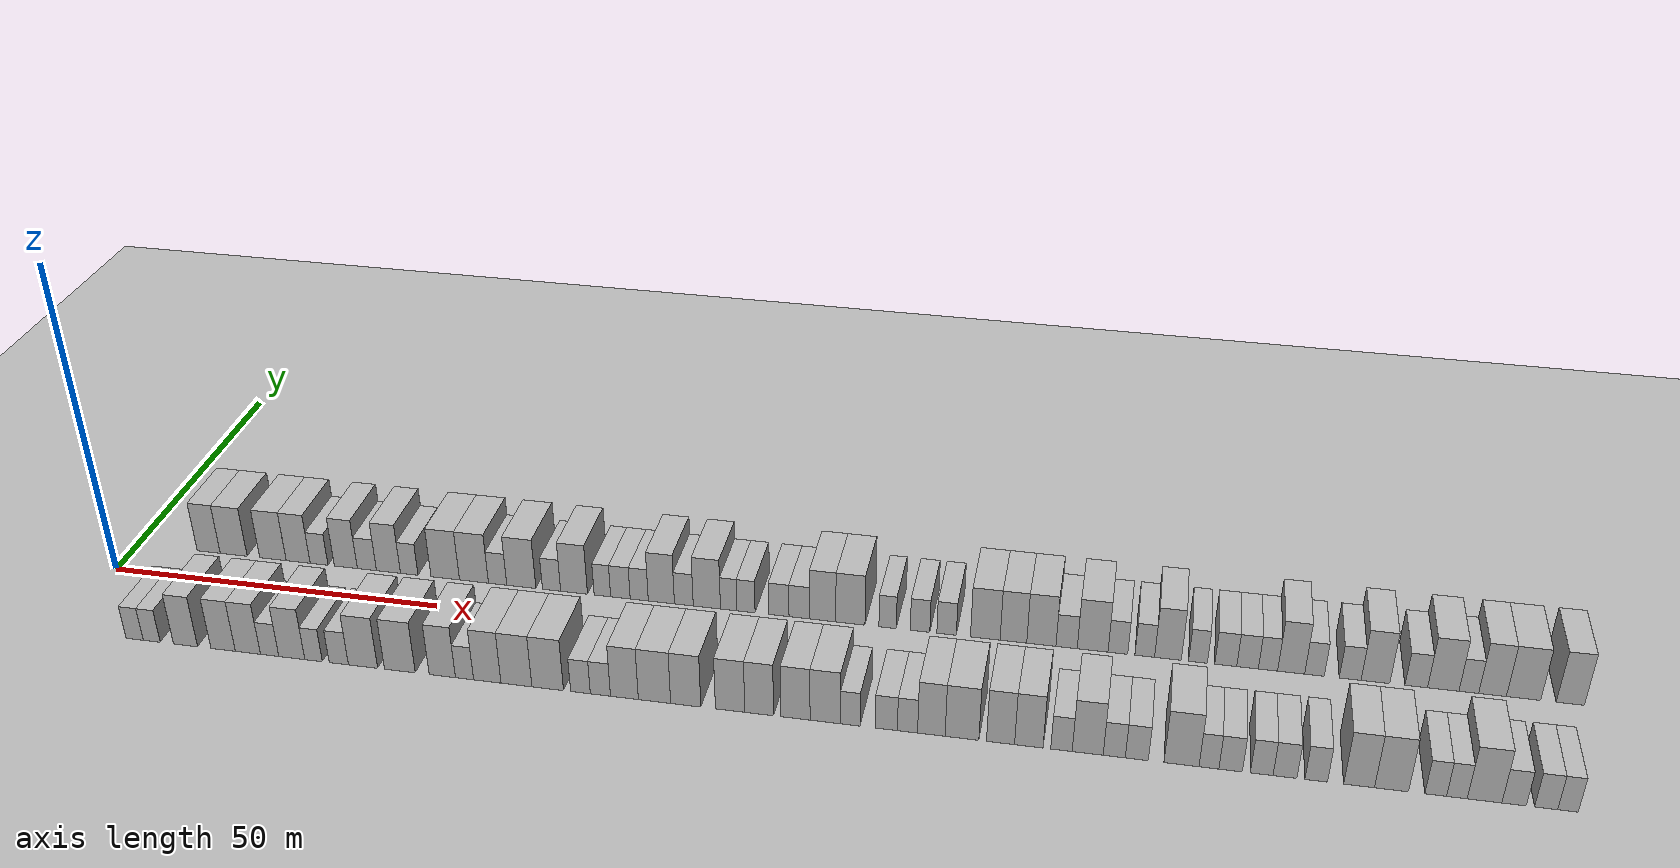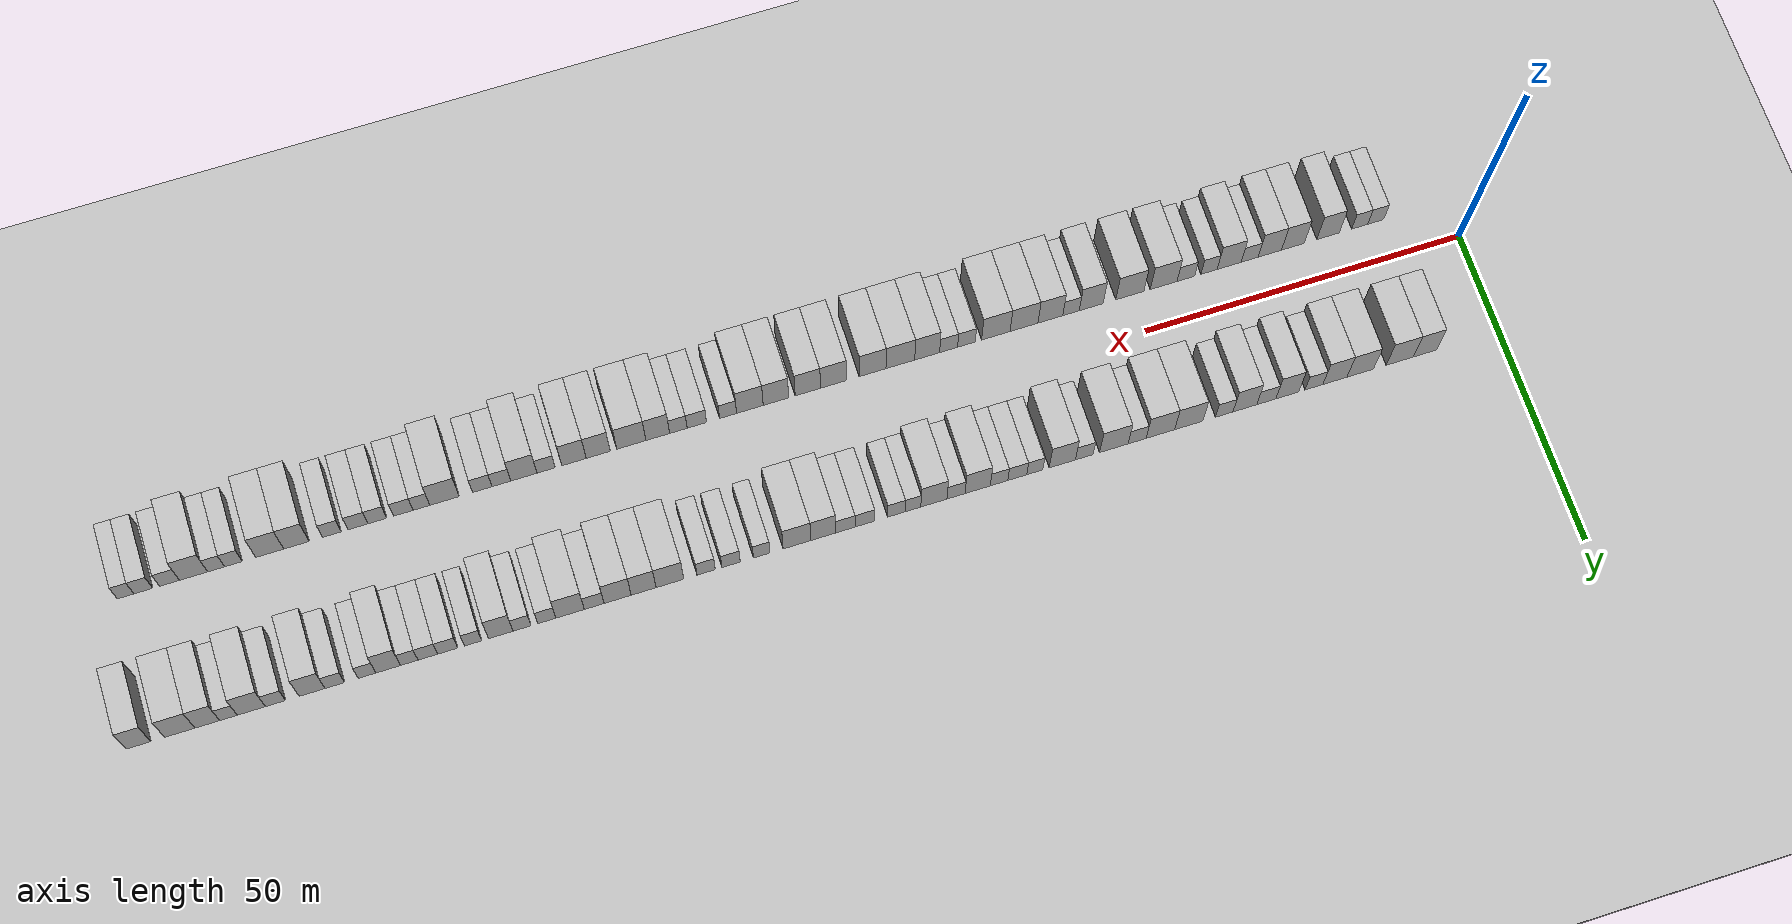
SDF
<?xml version="1.0" encoding="utf-8"?>

<sdf version="1.6">

   <world name="default">

      <gui fullscreen="0">

         <camera name="user_camera">

            <pose>-15 0 4.57585 0 0 0</pose>

            <view_controller>orbit</view_controller>

         </camera>

      </gui>

      <scene>

         <sky>

           <clouds>

             <speed>12</speed>

           </clouds>

         </sky>

         <ambient>0.4 0.4 0.4 1</ambient>

         <background>0.7 0.7 0.7 1</background>

         <shadows>1</shadows>

      </scene>

      <gravity>0 0 -9.8066</gravity>

      <magnetic_field>6e-06 2.3e-05 -4.2e-05</magnetic_field>

      <physics default="0" name="default_physics" type="ode">

         <ode>

            <solver>

               <type>quick</type>

               <iters>10</iters>

               <sor>1.0</sor>

               <use_dynamic_moi_rescaling>0</use_dynamic_moi_rescaling>

            </solver>

            <constraints>

               <cfm>0</cfm>

               <erp>0.2</erp>

               <contact_max_correcting_vel>100</contact_max_correcting_vel>

               <contact_surface_layer>0.001</contact_surface_layer>

            </constraints>

         </ode>

         <max_step_size>0.004</max_step_size>

         <real_time_factor>1</real_time_factor>

         <real_time_update_rate>250</real_time_update_rate>

      </physics>

      <light name="sun" type="directional">

         <cast_shadows>1</cast_shadows>

         <pose>0 0 10 0 0 0</pose>

         <diffuse>0.8 0.8 0.8 1</diffuse>

         <specular>0.2 0.2 0.2 1</specular>

         <attenuation>

            <range>1000</range>

            <constant>0.9</constant>

            <linear>0.01</linear>

            <quadratic>0.001</quadratic>

         </attenuation>

         <direction>-0.5 0.1 -0.9</direction>

      </light>

      <include>

         <name>ground_plane_1</name>

         <uri>model://HANNAS_ground_plane</uri>

         <pose>0 0 0  0 0 0</pose>

      </include>

      <include>

         <name>ground_plane_2</name>

         <uri>model://HANNAS_ground_plane</uri>

         <pose>100 0 0  0 0 0</pose>

      </include>

      <model name="building_1">

         <static>1</static>

         <pose frame="">11.8461 11.0000 0 0.000000 0.000000 1.570796</pose>

         <link name="link">

            <pose frame="">0 0 4.50 0 0 0</pose>

            <collision name="collision">

               <geometry>

                  <box>

                     <size>10.0000 3.6923 9.0000</size>

                  </box>

               </geometry>

               <max_contacts>10</max_contacts>

               <surface>

                  <contact>

                     <ode/>

                  </contact>

                  <bounce/>

                  <friction>

                     <torsional>

                        <ode/>

                     </torsional>

                     <ode/>

                  </friction>

               </surface>

            </collision>

            <visual name="visual">

               <cast_shadows>0</cast_shadows>

               <geometry>

                  <box>

                     <size>10.0000 3.6923 9.0000</size>

                  </box>

               </geometry>

               <material>

                  <script>

                     <uri>model://HANNAS_wall/materials/scripts</uri>

                     <uri>model://HANNAS_wall/materials/textures</uri>

                     <name>vrc/HANNAS_wall</name>

                  </script>

               </material>

            </visual>

            <self_collide>0</self_collide>

            <enable_wind>0</enable_wind>

            <kinematic>0</kinematic>

         </link>

      </model>

      <model name="building_2">

         <static>1</static>

         <pose frame="">15.8507 11.0000 0 0.000000 0.000000 1.570796</pose>

         <link name="link">

            <pose frame="">0 0 4.50 0 0 0</pose>

            <collision name="collision">

               <geometry>

                  <box>

                     <size>10.0000 4.3167 9.0000</size>

                  </box>

               </geometry>

               <max_contacts>10</max_contacts>

               <surface>

                  <contact>

                     <ode/>

                  </contact>

                  <bounce/>

                  <friction>

                     <torsional>

                        <ode/>

                     </torsional>

                     <ode/>

                  </friction>

               </surface>

            </collision>

            <visual name="visual">

               <cast_shadows>0</cast_shadows>

               <geometry>

                  <box>

                     <size>10.0000 4.3167 9.0000</size>

                  </box>

               </geometry>

               <material>

                  <script>

                     <uri>model://HANNAS_wall/materials/scripts</uri>

                     <uri>model://HANNAS_wall/materials/textures</uri>

                     <name>vrc/HANNAS_wall</name>

                  </script>

               </material>

            </visual>

            <self_collide>0</self_collide>

            <enable_wind>0</enable_wind>

            <kinematic>0</kinematic>

         </link>

      </model>

      <model name="building_3">

         <static>1</static>

         <pose frame="">22.1099 11.0000 0 0.000000 0.000000 1.570796</pose>

         <link name="link">

            <pose frame="">0 0 4.50 0 0 0</pose>

            <collision name="collision">

               <geometry>

                  <box>

                     <size>10.0000 4.2018 9.0000</size>

                  </box>

               </geometry>

               <max_contacts>10</max_contacts>

               <surface>

                  <contact>

                     <ode/>

                  </contact>

                  <bounce/>

                  <friction>

                     <torsional>

                        <ode/>

                     </torsional>

                     <ode/>

                  </friction>

               </surface>

            </collision>

            <visual name="visual">

               <cast_shadows>0</cast_shadows>

               <geometry>

                  <box>

                     <size>10.0000 4.2018 9.0000</size>

                  </box>

               </geometry>

               <material>

                  <script>

                     <uri>model://HANNAS_wall/materials/scripts</uri>

                     <uri>model://HANNAS_wall/materials/textures</uri>

                     <name>vrc/HANNAS_wall</name>

                  </script>

               </material>

            </visual>

            <self_collide>0</self_collide>

            <enable_wind>0</enable_wind>

            <kinematic>0</kinematic>

         </link>

      </model>

      <model name="building_4">

         <static>1</static>

         <pose frame="">26.1107 11.0000 0 0.000000 0.000000 1.570796</pose>

         <link name="link">

            <pose frame="">0 0 4.50 0 0 0</pose>

            <collision name="collision">

               <geometry>

                  <box>

                     <size>10.0000 3.7997 9.0000</size>

                  </box>

               </geometry>

               <max_contacts>10</max_contacts>

               <surface>

                  <contact>

                     <ode/>

                  </contact>

                  <bounce/>

                  <friction>

                     <torsional>

                        <ode/>

                     </torsional>

                     <ode/>

                  </friction>

               </surface>

            </collision>

            <visual name="visual">

               <cast_shadows>0</cast_shadows>

               <geometry>

                  <box>

                     <size>10.0000 3.7997 9.0000</size>

                  </box>

               </geometry>

               <material>

                  <script>

                     <uri>model://HANNAS_wall/materials/scripts</uri>

                     <uri>model://HANNAS_wall/materials/textures</uri>

                     <name>vrc/HANNAS_wall</name>

                  </script>

               </material>

            </visual>

            <self_collide>0</self_collide>

            <enable_wind>0</enable_wind>

            <kinematic>0</kinematic>

         </link>

      </model>

      <model name="building_5">

         <static>1</static>

         <pose frame="">29.4177 11.0000 0 0.000000 0.000000 1.570796</pose>

         <link name="link">

            <pose frame="">0 0 3.00 0 0 0</pose>

            <collision name="collision">

               <geometry>

                  <box>

                     <size>10.0000 2.8143 6.0000</size>

                  </box>

               </geometry>

               <max_contacts>10</max_contacts>

               <surface>

                  <contact>

                     <ode/>

                  </contact>

                  <bounce/>

                  <friction>

                     <torsional>

                        <ode/>

                     </torsional>

                     <ode/>

                  </friction>

               </surface>

            </collision>

            <visual name="visual">

               <cast_shadows>0</cast_shadows>

               <geometry>

                  <box>

                     <size>10.0000 2.8143 6.0000</size>

                  </box>

               </geometry>

               <material>

                  <script>

                     <uri>model://HANNAS_wall/materials/scripts</uri>

                     <uri>model://HANNAS_wall/materials/textures</uri>

                     <name>vrc/HANNAS_wall</name>

                  </script>

               </material>

            </visual>

            <self_collide>0</self_collide>

            <enable_wind>0</enable_wind>

            <kinematic>0</kinematic>

         </link>

      </model>

      <model name="building_6">

         <static>1</static>

         <pose frame="">33.6269 11.0000 0 0.000000 0.000000 1.570796</pose>

         <link name="link">

            <pose frame="">0 0 4.50 0 0 0</pose>

            <collision name="collision">

               <geometry>

                  <box>

                     <size>10.0000 3.6042 9.0000</size>

                  </box>

               </geometry>

               <max_contacts>10</max_contacts>

               <surface>

                  <contact>

                     <ode/>

                  </contact>

                  <bounce/>

                  <friction>

                     <torsional>

                        <ode/>

                     </torsional>

                     <ode/>

                  </friction>

               </surface>

            </collision>

            <visual name="visual">

               <cast_shadows>0</cast_shadows>

               <geometry>

                  <box>

                     <size>10.0000 3.6042 9.0000</size>

                  </box>

               </geometry>

               <material>

                  <script>

                     <uri>model://HANNAS_wall/materials/scripts</uri>

                     <uri>model://HANNAS_wall/materials/textures</uri>

                     <name>vrc/HANNAS_wall</name>

                  </script>

               </material>

            </visual>

            <self_collide>0</self_collide>

            <enable_wind>0</enable_wind>

            <kinematic>0</kinematic>

         </link>

      </model>

      <model name="building_7">

         <static>1</static>

         <pose frame="">36.9258 11.0000 0 0.000000 0.000000 1.570796</pose>

         <link name="link">

            <pose frame="">0 0 3.00 0 0 0</pose>

            <collision name="collision">

               <geometry>

                  <box>

                     <size>10.0000 2.9936 6.0000</size>

                  </box>

               </geometry>

               <max_contacts>10</max_contacts>

               <surface>

                  <contact>

                     <ode/>

                  </contact>

                  <bounce/>

                  <friction>

                     <torsional>

                        <ode/>

                     </torsional>

                     <ode/>

                  </friction>

               </surface>

            </collision>

            <visual name="visual">

               <cast_shadows>0</cast_shadows>

               <geometry>

                  <box>

                     <size>10.0000 2.9936 6.0000</size>

                  </box>

               </geometry>

               <material>

                  <script>

                     <uri>model://HANNAS_wall/materials/scripts</uri>

                     <uri>model://HANNAS_wall/materials/textures</uri>

                     <name>vrc/HANNAS_wall</name>

                  </script>

               </material>

            </visual>

            <self_collide>0</self_collide>

            <enable_wind>0</enable_wind>

            <kinematic>0</kinematic>

         </link>

      </model>

      <model name="building_8">

         <static>1</static>

         <pose frame="">40.2935 11.0000 0 0.000000 0.000000 1.570796</pose>

         <link name="link">

            <pose frame="">0 0 4.50 0 0 0</pose>

            <collision name="collision">

               <geometry>

                  <box>

                     <size>10.0000 3.7417 9.0000</size>

                  </box>

               </geometry>

               <max_contacts>10</max_contacts>

               <surface>

                  <contact>

                     <ode/>

                  </contact>

                  <bounce/>

                  <friction>

                     <torsional>

                        <ode/>

                     </torsional>

                     <ode/>

                  </friction>

               </surface>

            </collision>

            <visual name="visual">

               <cast_shadows>0</cast_shadows>

               <geometry>

                  <box>

                     <size>10.0000 3.7417 9.0000</size>

                  </box>

               </geometry>

               <material>

                  <script>

                     <uri>model://HANNAS_wall/materials/scripts</uri>

                     <uri>model://HANNAS_wall/materials/textures</uri>

                     <name>vrc/HANNAS_wall</name>

                  </script>

               </material>

            </visual>

            <self_collide>0</self_collide>

            <enable_wind>0</enable_wind>

            <kinematic>0</kinematic>

         </link>

      </model>

      <model name="building_9">

         <static>1</static>

         <pose frame="">43.5288 11.0000 0 0.000000 0.000000 1.570796</pose>

         <link name="link">

            <pose frame="">0 0 3.00 0 0 0</pose>

            <collision name="collision">

               <geometry>

                  <box>

                     <size>10.0000 2.7289 6.0000</size>

                  </box>

               </geometry>

               <max_contacts>10</max_contacts>

               <surface>

                  <contact>

                     <ode/>

                  </contact>

                  <bounce/>

                  <friction>

                     <torsional>

                        <ode/>

                     </torsional>

                     <ode/>

                  </friction>

               </surface>

            </collision>

            <visual name="visual">

               <cast_shadows>0</cast_shadows>

               <geometry>

                  <box>

                     <size>10.0000 2.7289 6.0000</size>

                  </box>

               </geometry>

               <material>

                  <script>

                     <uri>model://HANNAS_wall/materials/scripts</uri>

                     <uri>model://HANNAS_wall/materials/textures</uri>

                     <name>vrc/HANNAS_wall</name>

                  </script>

               </material>

            </visual>

            <self_collide>0</self_collide>

            <enable_wind>0</enable_wind>

            <kinematic>0</kinematic>

         </link>

      </model>

      <model name="building_10">

         <static>1</static>

         <pose frame="">49.0889 11.0000 0 0.000000 0.000000 1.570796</pose>

         <link name="link">

            <pose frame="">0 0 4.50 0 0 0</pose>

            <collision name="collision">

               <geometry>

                  <box>

                     <size>10.0000 4.3914 9.0000</size>

                  </box>

               </geometry>

               <max_contacts>10</max_contacts>

               <surface>

                  <contact>

                     <ode/>

                  </contact>

                  <bounce/>

                  <friction>

                     <torsional>

                        <ode/>

                     </torsional>

                     <ode/>

                  </friction>

               </surface>

            </collision>

            <visual name="visual">

               <cast_shadows>0</cast_shadows>

               <geometry>

                  <box>

                     <size>10.0000 4.3914 9.0000</size>

                  </box>

               </geometry>

               <material>

                  <script>

                     <uri>model://HANNAS_wall/materials/scripts</uri>

                     <uri>model://HANNAS_wall/materials/textures</uri>

                     <name>vrc/HANNAS_wall</name>

                  </script>

               </material>

            </visual>

            <self_collide>0</self_collide>

            <enable_wind>0</enable_wind>

            <kinematic>0</kinematic>

         </link>

      </model>

      <model name="building_11">

         <static>1</static>

         <pose frame="">53.5104 11.0000 0 0.000000 0.000000 1.570796</pose>

         <link name="link">

            <pose frame="">0 0 4.50 0 0 0</pose>

            <collision name="collision">

               <geometry>

                  <box>

                     <size>10.0000 4.4515 9.0000</size>

                  </box>

               </geometry>

               <max_contacts>10</max_contacts>

               <surface>

                  <contact>

                     <ode/>

                  </contact>

                  <bounce/>

                  <friction>

                     <torsional>

                        <ode/>

                     </torsional>

                     <ode/>

                  </friction>

               </surface>

            </collision>

            <visual name="visual">

               <cast_shadows>0</cast_shadows>

               <geometry>

                  <box>

                     <size>10.0000 4.4515 9.0000</size>

                  </box>

               </geometry>

               <material>

                  <script>

                     <uri>model://HANNAS_wall/materials/scripts</uri>

                     <uri>model://HANNAS_wall/materials/textures</uri>

                     <name>vrc/HANNAS_wall</name>

                  </script>

               </material>

            </visual>

            <self_collide>0</self_collide>

            <enable_wind>0</enable_wind>

            <kinematic>0</kinematic>

         </link>

      </model>

      <model name="building_12">

         <static>1</static>

         <pose frame="">57.1330 11.0000 0 0.000000 0.000000 1.570796</pose>

         <link name="link">

            <pose frame="">0 0 3.00 0 0 0</pose>

            <collision name="collision">

               <geometry>

                  <box>

                     <size>10.0000 2.7939 6.0000</size>

                  </box>

               </geometry>

               <max_contacts>10</max_contacts>

               <surface>

                  <contact>

                     <ode/>

                  </contact>

                  <bounce/>

                  <friction>

                     <torsional>

                        <ode/>

                     </torsional>

                     <ode/>

                  </friction>

               </surface>

            </collision>

            <visual name="visual">

               <cast_shadows>0</cast_shadows>

               <geometry>

                  <box>

                     <size>10.0000 2.7939 6.0000</size>

                  </box>

               </geometry>

               <material>

                  <script>

                     <uri>model://HANNAS_wall/materials/scripts</uri>

                     <uri>model://HANNAS_wall/materials/textures</uri>

                     <name>vrc/HANNAS_wall</name>

                  </script>

               </material>

            </visual>

            <self_collide>0</self_collide>

            <enable_wind>0</enable_wind>

            <kinematic>0</kinematic>

         </link>

      </model>

      <model name="building_13">

         <static>1</static>

         <pose frame="">60.7514 11.0000 0 0.000000 0.000000 1.570796</pose>

         <link name="link">

            <pose frame="">0 0 4.50 0 0 0</pose>

            <collision name="collision">

               <geometry>

                  <box>

                     <size>10.0000 4.4428 9.0000</size>

                  </box>

               </geometry>

               <max_contacts>10</max_contacts>

               <surface>

                  <contact>

                     <ode/>

                  </contact>

                  <bounce/>

                  <friction>

                     <torsional>

                        <ode/>

                     </torsional>

                     <ode/>

                  </friction>

               </surface>

            </collision>

            <visual name="visual">

               <cast_shadows>0</cast_shadows>

               <geometry>

                  <box>

                     <size>10.0000 4.4428 9.0000</size>

                  </box>

               </geometry>

               <material>

                  <script>

                     <uri>model://HANNAS_wall/materials/scripts</uri>

                     <uri>model://HANNAS_wall/materials/textures</uri>

                     <name>vrc/HANNAS_wall</name>

                  </script>

               </material>

            </visual>

            <self_collide>0</self_collide>

            <enable_wind>0</enable_wind>

            <kinematic>0</kinematic>

         </link>

      </model>

      <model name="building_14">

         <static>1</static>

         <pose frame="">65.3488 11.0000 0 0.000000 0.000000 1.570796</pose>

         <link name="link">

            <pose frame="">0 0 3.00 0 0 0</pose>

            <collision name="collision">

               <geometry>

                  <box>

                     <size>10.0000 2.7521 6.0000</size>

                  </box>

               </geometry>

               <max_contacts>10</max_contacts>

               <surface>

                  <contact>

                     <ode/>

                  </contact>

                  <bounce/>

                  <friction>

                     <torsional>

                        <ode/>

                     </torsional>

                     <ode/>

                  </friction>

               </surface>

            </collision>

            <visual name="visual">

               <cast_shadows>0</cast_shadows>

               <geometry>

                  <box>

                     <size>10.0000 2.7521 6.0000</size>

                  </box>

               </geometry>

               <material>

                  <script>

                     <uri>model://HANNAS_wall/materials/scripts</uri>

                     <uri>model://HANNAS_wall/materials/textures</uri>

                     <name>vrc/HANNAS_wall</name>

                  </script>

               </material>

            </visual>

            <self_collide>0</self_collide>

            <enable_wind>0</enable_wind>

            <kinematic>0</kinematic>

         </link>

      </model>

      <model name="building_15">

         <static>1</static>

         <pose frame="">68.7537 11.0000 0 0.000000 0.000000 1.570796</pose>

         <link name="link">

            <pose frame="">0 0 4.50 0 0 0</pose>

            <collision name="collision">

               <geometry>

                  <box>

                     <size>10.0000 4.0577 9.0000</size>

                  </box>

               </geometry>

               <max_contacts>10</max_contacts>

               <surface>

                  <contact>

                     <ode/>

                  </contact>

                  <bounce/>

                  <friction>

                     <torsional>

                        <ode/>

                     </torsional>

                     <ode/>

                  </friction>

               </surface>

            </collision>

            <visual name="visual">

               <cast_shadows>0</cast_shadows>

               <geometry>

                  <box>

                     <size>10.0000 4.0577 9.0000</size>

                  </box>

               </geometry>

               <material>

                  <script>

                     <uri>model://HANNAS_wall/materials/scripts</uri>

                     <uri>model://HANNAS_wall/materials/textures</uri>

                     <name>vrc/HANNAS_wall</name>

                  </script>

               </material>

            </visual>

            <self_collide>0</self_collide>

            <enable_wind>0</enable_wind>

            <kinematic>0</kinematic>

         </link>

      </model>

      <model name="building_16">

         <static>1</static>

         <pose frame="">73.0201 11.0000 0 0.000000 0.000000 1.570796</pose>

         <link name="link">

            <pose frame="">0 0 3.00 0 0 0</pose>

            <collision name="collision">

               <geometry>

                  <box>

                     <size>10.0000 2.4750 6.0000</size>

                  </box>

               </geometry>

               <max_contacts>10</max_contacts>

               <surface>

                  <contact>

                     <ode/>

                  </contact>

                  <bounce/>

                  <friction>

                     <torsional>

                        <ode/>

                     </torsional>

                     <ode/>

                  </friction>

               </surface>

            </collision>

            <visual name="visual">

               <cast_shadows>0</cast_shadows>

               <geometry>

                  <box>

                     <size>10.0000 2.4750 6.0000</size>

                  </box>

               </geometry>

               <material>

                  <script>

                     <uri>model://HANNAS_wall/materials/scripts</uri>

                     <uri>model://HANNAS_wall/materials/textures</uri>

                     <name>vrc/HANNAS_wall</name>

                  </script>

               </material>

            </visual>

            <self_collide>0</self_collide>

            <enable_wind>0</enable_wind>

            <kinematic>0</kinematic>

         </link>

      </model>

      <model name="building_17">

         <static>1</static>

         <pose frame="">75.7228 11.0000 0 0.000000 0.000000 1.570796</pose>

         <link name="link">

            <pose frame="">0 0 3.00 0 0 0</pose>

            <collision name="collision">

               <geometry>

                  <box>

                     <size>10.0000 2.9305 6.0000</size>

                  </box>

               </geometry>

               <max_contacts>10</max_contacts>

               <surface>

                  <contact>

                     <ode/>

                  </contact>

                  <bounce/>

                  <friction>

                     <torsional>

                        <ode/>

                     </torsional>

                     <ode/>

                  </friction>

               </surface>

            </collision>

            <visual name="visual">

               <cast_shadows>0</cast_shadows>

               <geometry>

                  <box>

                     <size>10.0000 2.9305 6.0000</size>

                  </box>

               </geometry>

               <material>

                  <script>

                     <uri>model://HANNAS_wall/materials/scripts</uri>

                     <uri>model://HANNAS_wall/materials/textures</uri>

                     <name>vrc/HANNAS_wall</name>

                  </script>

               </material>

            </visual>

            <self_collide>0</self_collide>

            <enable_wind>0</enable_wind>

            <kinematic>0</kinematic>

         </link>

      </model>

      <model name="building_18">

         <static>1</static>

         <pose frame="">78.5389 11.0000 0 0.000000 0.000000 1.570796</pose>

         <link name="link">

            <pose frame="">0 0 3.00 0 0 0</pose>

            <collision name="collision">

               <geometry>

                  <box>

                     <size>10.0000 2.7016 6.0000</size>

                  </box>

               </geometry>

               <max_contacts>10</max_contacts>

               <surface>

                  <contact>

                     <ode/>

                  </contact>

                  <bounce/>

                  <friction>

                     <torsional>

                        <ode/>

                     </torsional>

                     <ode/>

                  </friction>

               </surface>

            </collision>

            <visual name="visual">

               <cast_shadows>0</cast_shadows>

               <geometry>

                  <box>

                     <size>10.0000 2.7016 6.0000</size>

                  </box>

               </geometry>

               <material>

                  <script>

                     <uri>model://HANNAS_wall/materials/scripts</uri>

                     <uri>model://HANNAS_wall/materials/textures</uri>

                     <name>vrc/HANNAS_wall</name>

                  </script>

               </material>

            </visual>

            <self_collide>0</self_collide>

            <enable_wind>0</enable_wind>

            <kinematic>0</kinematic>

         </link>

      </model>

      <model name="building_19">

         <static>1</static>

         <pose frame="">81.8342 11.0000 0 0.000000 0.000000 1.570796</pose>

         <link name="link">

            <pose frame="">0 0 4.50 0 0 0</pose>

            <collision name="collision">

               <geometry>

                  <box>

                     <size>10.0000 3.8890 9.0000</size>

                  </box>

               </geometry>

               <max_contacts>10</max_contacts>

               <surface>

                  <contact>

                     <ode/>

                  </contact>

                  <bounce/>

                  <friction>

                     <torsional>

                        <ode/>

                     </torsional>

                     <ode/>

                  </friction>

               </surface>

            </collision>

            <visual name="visual">

               <cast_shadows>0</cast_shadows>

               <geometry>

                  <box>

                     <size>10.0000 3.8890 9.0000</size>

                  </box>

               </geometry>

               <material>

                  <script>

                     <uri>model://HANNAS_wall/materials/scripts</uri>

                     <uri>model://HANNAS_wall/materials/textures</uri>

                     <name>vrc/HANNAS_wall</name>

                  </script>

               </material>

            </visual>

            <self_collide>0</self_collide>

            <enable_wind>0</enable_wind>

            <kinematic>0</kinematic>

         </link>

      </model>

      <model name="building_20">

         <static>1</static>

         <pose frame="">85.1712 11.0000 0 0.000000 0.000000 1.570796</pose>

         <link name="link">

            <pose frame="">0 0 3.00 0 0 0</pose>

            <collision name="collision">

               <geometry>

                  <box>

                     <size>10.0000 2.7850 6.0000</size>

                  </box>

               </geometry>

               <max_contacts>10</max_contacts>

               <surface>

                  <contact>

                     <ode/>

                  </contact>

                  <bounce/>

                  <friction>

                     <torsional>

                        <ode/>

                     </torsional>

                     <ode/>

                  </friction>

               </surface>

            </collision>

            <visual name="visual">

               <cast_shadows>0</cast_shadows>

               <geometry>

                  <box>

                     <size>10.0000 2.7850 6.0000</size>

                  </box>

               </geometry>

               <material>

                  <script>

                     <uri>model://HANNAS_wall/materials/scripts</uri>

                     <uri>model://HANNAS_wall/materials/textures</uri>

                     <name>vrc/HANNAS_wall</name>

                  </script>

               </material>

            </visual>

            <self_collide>0</self_collide>

            <enable_wind>0</enable_wind>

            <kinematic>0</kinematic>

         </link>

      </model>

      <model name="building_21">

         <static>1</static>

         <pose frame="">88.5730 11.0000 0 0.000000 0.000000 1.570796</pose>

         <link name="link">

            <pose frame="">0 0 4.50 0 0 0</pose>

            <collision name="collision">

               <geometry>

                  <box>

                     <size>10.0000 4.0187 9.0000</size>

                  </box>

               </geometry>

               <max_contacts>10</max_contacts>

               <surface>

                  <contact>

                     <ode/>

                  </contact>

                  <bounce/>

                  <friction>

                     <torsional>

                        <ode/>

                     </torsional>

                     <ode/>

                  </friction>

               </surface>

            </collision>

            <visual name="visual">

               <cast_shadows>0</cast_shadows>

               <geometry>

                  <box>

                     <size>10.0000 4.0187 9.0000</size>

                  </box>

               </geometry>

               <material>

                  <script>

                     <uri>model://HANNAS_wall/materials/scripts</uri>

                     <uri>model://HANNAS_wall/materials/textures</uri>

                     <name>vrc/HANNAS_wall</name>

                  </script>

               </material>

            </visual>

            <self_collide>0</self_collide>

            <enable_wind>0</enable_wind>

            <kinematic>0</kinematic>

         </link>

      </model>

      <model name="building_22">

         <static>1</static>

         <pose frame="">91.7902 11.0000 0 0.000000 0.000000 1.570796</pose>

         <link name="link">

            <pose frame="">0 0 3.00 0 0 0</pose>

            <collision name="collision">

               <geometry>

                  <box>

                     <size>10.0000 2.4156 6.0000</size>

                  </box>

               </geometry>

               <max_contacts>10</max_contacts>

               <surface>

                  <contact>

                     <ode/>

                  </contact>

                  <bounce/>

                  <friction>

                     <torsional>

                        <ode/>

                     </torsional>

                     <ode/>

                  </friction>

               </surface>

            </collision>

            <visual name="visual">

               <cast_shadows>0</cast_shadows>

               <geometry>

                  <box>

                     <size>10.0000 2.4156 6.0000</size>

                  </box>

               </geometry>

               <material>

                  <script>

                     <uri>model://HANNAS_wall/materials/scripts</uri>

                     <uri>model://HANNAS_wall/materials/textures</uri>

                     <name>vrc/HANNAS_wall</name>

                  </script>

               </material>

            </visual>

            <self_collide>0</self_collide>

            <enable_wind>0</enable_wind>

            <kinematic>0</kinematic>

         </link>

      </model>

      <model name="building_23">

         <static>1</static>

         <pose frame="">94.3314 11.0000 0 0.000000 0.000000 1.570796</pose>

         <link name="link">

            <pose frame="">0 0 3.00 0 0 0</pose>

            <collision name="collision">

               <geometry>

                  <box>

                     <size>10.0000 2.6670 6.0000</size>

                  </box>

               </geometry>

               <max_contacts>10</max_contacts>

               <surface>

                  <contact>

                     <ode/>

                  </contact>

                  <bounce/>

                  <friction>

                     <torsional>

                        <ode/>

                     </torsional>

                     <ode/>

                  </friction>

               </surface>

            </collision>

            <visual name="visual">

               <cast_shadows>0</cast_shadows>

               <geometry>

                  <box>

                     <size>10.0000 2.6670 6.0000</size>

                  </box>

               </geometry>

               <material>

                  <script>

                     <uri>model://HANNAS_wall/materials/scripts</uri>

                     <uri>model://HANNAS_wall/materials/textures</uri>

                     <name>vrc/HANNAS_wall</name>

                  </script>

               </material>

            </visual>

            <self_collide>0</self_collide>

            <enable_wind>0</enable_wind>

            <kinematic>0</kinematic>

         </link>

      </model>

      <model name="building_24">

         <static>1</static>

         <pose frame="">99.1431 11.0000 0 0.000000 0.000000 1.570796</pose>

         <link name="link">

            <pose frame="">0 0 3.00 0 0 0</pose>

            <collision name="collision">

               <geometry>

                  <box>

                     <size>10.0000 2.9564 6.0000</size>

                  </box>

               </geometry>

               <max_contacts>10</max_contacts>

               <surface>

                  <contact>

                     <ode/>

                  </contact>

                  <bounce/>

                  <friction>

                     <torsional>

                        <ode/>

                     </torsional>

                     <ode/>

                  </friction>

               </surface>

            </collision>

            <visual name="visual">

               <cast_shadows>0</cast_shadows>

               <geometry>

                  <box>

                     <size>10.0000 2.9564 6.0000</size>

                  </box>

               </geometry>

               <material>

                  <script>

                     <uri>model://HANNAS_wall/materials/scripts</uri>

                     <uri>model://HANNAS_wall/materials/textures</uri>

                     <name>vrc/HANNAS_wall</name>

                  </script>

               </material>

            </visual>

            <self_collide>0</self_collide>

            <enable_wind>0</enable_wind>

            <kinematic>0</kinematic>

         </link>

      </model>

      <model name="building_25">

         <static>1</static>

         <pose frame="">102.1106 11.0000 0 0.000000 0.000000 1.570796</pose>

         <link name="link">

            <pose frame="">0 0 3.00 0 0 0</pose>

            <collision name="collision">

               <geometry>

                  <box>

                     <size>10.0000 2.9786 6.0000</size>

                  </box>

               </geometry>

               <max_contacts>10</max_contacts>

               <surface>

                  <contact>

                     <ode/>

                  </contact>

                  <bounce/>

                  <friction>

                     <torsional>

                        <ode/>

                     </torsional>

                     <ode/>

                  </friction>

               </surface>

            </collision>

            <visual name="visual">

               <cast_shadows>0</cast_shadows>

               <geometry>

                  <box>

                     <size>10.0000 2.9786 6.0000</size>

                  </box>

               </geometry>

               <material>

                  <script>

                     <uri>model://HANNAS_wall/materials/scripts</uri>

                     <uri>model://HANNAS_wall/materials/textures</uri>

                     <name>vrc/HANNAS_wall</name>

                  </script>

               </material>

            </visual>

            <self_collide>0</self_collide>

            <enable_wind>0</enable_wind>

            <kinematic>0</kinematic>

         </link>

      </model>

      <model name="building_26">

         <static>1</static>

         <pose frame="">105.5033 11.0000 0 0.000000 0.000000 1.570796</pose>

         <link name="link">

            <pose frame="">0 0 4.50 0 0 0</pose>

            <collision name="collision">

               <geometry>

                  <box>

                     <size>10.0000 3.8068 9.0000</size>

                  </box>

               </geometry>

               <max_contacts>10</max_contacts>

               <surface>

                  <contact>

                     <ode/>

                  </contact>

                  <bounce/>

                  <friction>

                     <torsional>

                        <ode/>

                     </torsional>

                     <ode/>

                  </friction>

               </surface>

            </collision>

            <visual name="visual">

               <cast_shadows>0</cast_shadows>

               <geometry>

                  <box>

                     <size>10.0000 3.8068 9.0000</size>

                  </box>

               </geometry>

               <material>

                  <script>

                     <uri>model://HANNAS_wall/materials/scripts</uri>

                     <uri>model://HANNAS_wall/materials/textures</uri>

                     <name>vrc/HANNAS_wall</name>

                  </script>

               </material>

            </visual>

            <self_collide>0</self_collide>

            <enable_wind>0</enable_wind>

            <kinematic>0</kinematic>

         </link>

      </model>

      <model name="building_27">

         <static>1</static>

         <pose frame="">109.5099 11.0000 0 0.000000 0.000000 1.570796</pose>

         <link name="link">

            <pose frame="">0 0 4.50 0 0 0</pose>

            <collision name="collision">

               <geometry>

                  <box>

                     <size>10.0000 4.2064 9.0000</size>

                  </box>

               </geometry>

               <max_contacts>10</max_contacts>

               <surface>

                  <contact>

                     <ode/>

                  </contact>

                  <bounce/>

                  <friction>

                     <torsional>

                        <ode/>

                     </torsional>

                     <ode/>

                  </friction>

               </surface>

            </collision>

            <visual name="visual">

               <cast_shadows>0</cast_shadows>

               <geometry>

                  <box>

                     <size>10.0000 4.2064 9.0000</size>

                  </box>

               </geometry>

               <material>

                  <script>

                     <uri>model://HANNAS_wall/materials/scripts</uri>

                     <uri>model://HANNAS_wall/materials/textures</uri>

                     <name>vrc/HANNAS_wall</name>

                  </script>

               </material>

            </visual>

            <self_collide>0</self_collide>

            <enable_wind>0</enable_wind>

            <kinematic>0</kinematic>

         </link>

      </model>

      <model name="building_28">

         <static>1</static>

         <pose frame="">114.8620 11.0000 0 0.000000 0.000000 1.570796</pose>

         <link name="link">

            <pose frame="">0 0 3.00 0 0 0</pose>

            <collision name="collision">

               <geometry>

                  <box>

                     <size>10.0000 2.4978 6.0000</size>

                  </box>

               </geometry>

               <max_contacts>10</max_contacts>

               <surface>

                  <contact>

                     <ode/>

                  </contact>

                  <bounce/>

                  <friction>

                     <torsional>

                        <ode/>

                     </torsional>

                     <ode/>

                  </friction>

               </surface>

            </collision>

            <visual name="visual">

               <cast_shadows>0</cast_shadows>

               <geometry>

                  <box>

                     <size>10.0000 2.4978 6.0000</size>

                  </box>

               </geometry>

               <material>

                  <script>

                     <uri>model://HANNAS_wall/materials/scripts</uri>

                     <uri>model://HANNAS_wall/materials/textures</uri>

                     <name>vrc/HANNAS_wall</name>

                  </script>

               </material>

            </visual>

            <self_collide>0</self_collide>

            <enable_wind>0</enable_wind>

            <kinematic>0</kinematic>

         </link>

      </model>

      <model name="building_29">

         <static>1</static>

         <pose frame="">119.5008 11.0000 0 0.000000 0.000000 1.570796</pose>

         <link name="link">

            <pose frame="">0 0 3.00 0 0 0</pose>

            <collision name="collision">

               <geometry>

                  <box>

                     <size>10.0000 2.7798 6.0000</size>

                  </box>

               </geometry>

               <max_contacts>10</max_contacts>

               <surface>

                  <contact>

                     <ode/>

                  </contact>

                  <bounce/>

                  <friction>

                     <torsional>

                        <ode/>

                     </torsional>

                     <ode/>

                  </friction>

               </surface>

            </collision>

            <visual name="visual">

               <cast_shadows>0</cast_shadows>

               <geometry>

                  <box>

                     <size>10.0000 2.7798 6.0000</size>

                  </box>

               </geometry>

               <material>

                  <script>

                     <uri>model://HANNAS_wall/materials/scripts</uri>

                     <uri>model://HANNAS_wall/materials/textures</uri>

                     <name>vrc/HANNAS_wall</name>

                  </script>

               </material>

            </visual>

            <self_collide>0</self_collide>

            <enable_wind>0</enable_wind>

            <kinematic>0</kinematic>

         </link>

      </model>

      <model name="building_30">

         <static>1</static>

         <pose frame="">123.2733 11.0000 0 0.000000 0.000000 1.570796</pose>

         <link name="link">

            <pose frame="">0 0 3.00 0 0 0</pose>

            <collision name="collision">

               <geometry>

                  <box>

                     <size>10.0000 2.7651 6.0000</size>

                  </box>

               </geometry>

               <max_contacts>10</max_contacts>

               <surface>

                  <contact>

                     <ode/>

                  </contact>

                  <bounce/>

                  <friction>

                     <torsional>

                        <ode/>

                     </torsional>

                     <ode/>

                  </friction>

               </surface>

            </collision>

            <visual name="visual">

               <cast_shadows>0</cast_shadows>

               <geometry>

                  <box>

                     <size>10.0000 2.7651 6.0000</size>

                  </box>

               </geometry>

               <material>

                  <script>

                     <uri>model://HANNAS_wall/materials/scripts</uri>

                     <uri>model://HANNAS_wall/materials/textures</uri>

                     <name>vrc/HANNAS_wall</name>

                  </script>

               </material>

            </visual>

            <self_collide>0</self_collide>

            <enable_wind>0</enable_wind>

            <kinematic>0</kinematic>

         </link>

      </model>

      <model name="building_31">

         <static>1</static>

         <pose frame="">128.7445 11.0000 0 0.000000 0.000000 1.570796</pose>

         <link name="link">

            <pose frame="">0 0 4.50 0 0 0</pose>

            <collision name="collision">

               <geometry>

                  <box>

                     <size>10.0000 4.1774 9.0000</size>

                  </box>

               </geometry>

               <max_contacts>10</max_contacts>

               <surface>

                  <contact>

                     <ode/>

                  </contact>

                  <bounce/>

                  <friction>

                     <torsional>

                        <ode/>

                     </torsional>

                     <ode/>

                  </friction>

               </surface>

            </collision>

            <visual name="visual">

               <cast_shadows>0</cast_shadows>

               <geometry>

                  <box>

                     <size>10.0000 4.1774 9.0000</size>

                  </box>

               </geometry>

               <material>

                  <script>

                     <uri>model://HANNAS_wall/materials/scripts</uri>

                     <uri>model://HANNAS_wall/materials/textures</uri>

                     <name>vrc/HANNAS_wall</name>

                  </script>

               </material>

            </visual>

            <self_collide>0</self_collide>

            <enable_wind>0</enable_wind>

            <kinematic>0</kinematic>

         </link>

      </model>

      <model name="building_32">

         <static>1</static>

         <pose frame="">132.7056 11.0000 0 0.000000 0.000000 1.570796</pose>

         <link name="link">

            <pose frame="">0 0 4.50 0 0 0</pose>

            <collision name="collision">

               <geometry>

                  <box>

                     <size>10.0000 3.7448 9.0000</size>

                  </box>

               </geometry>

               <max_contacts>10</max_contacts>

               <surface>

                  <contact>

                     <ode/>

                  </contact>

                  <bounce/>

                  <friction>

                     <torsional>

                        <ode/>

                     </torsional>

                     <ode/>

                  </friction>

               </surface>

            </collision>

            <visual name="visual">

               <cast_shadows>0</cast_shadows>

               <geometry>

                  <box>

                     <size>10.0000 3.7448 9.0000</size>

                  </box>

               </geometry>

               <material>

                  <script>

                     <uri>model://HANNAS_wall/materials/scripts</uri>

                     <uri>model://HANNAS_wall/materials/textures</uri>

                     <name>vrc/HANNAS_wall</name>

                  </script>

               </material>

            </visual>

            <self_collide>0</self_collide>

            <enable_wind>0</enable_wind>

            <kinematic>0</kinematic>

         </link>

      </model>

      <model name="building_33">

         <static>1</static>

         <pose frame="">136.6196 11.0000 0 0.000000 0.000000 1.570796</pose>

         <link name="link">

            <pose frame="">0 0 4.50 0 0 0</pose>

            <collision name="collision">

               <geometry>

                  <box>

                     <size>10.0000 4.0831 9.0000</size>

                  </box>

               </geometry>

               <max_contacts>10</max_contacts>

               <surface>

                  <contact>

                     <ode/>

                  </contact>

                  <bounce/>

                  <friction>

                     <torsional>

                        <ode/>

                     </torsional>

                     <ode/>

                  </friction>

               </surface>

            </collision>

            <visual name="visual">

               <cast_shadows>0</cast_shadows>

               <geometry>

                  <box>

                     <size>10.0000 4.0831 9.0000</size>

                  </box>

               </geometry>

               <material>

                  <script>

                     <uri>model://HANNAS_wall/materials/scripts</uri>

                     <uri>model://HANNAS_wall/materials/textures</uri>

                     <name>vrc/HANNAS_wall</name>

                  </script>

               </material>

            </visual>

            <self_collide>0</self_collide>

            <enable_wind>0</enable_wind>

            <kinematic>0</kinematic>

         </link>

      </model>

      <model name="building_34">

         <static>1</static>

         <pose frame="">140.1414 11.0000 0 0.000000 0.000000 1.570796</pose>

         <link name="link">

            <pose frame="">0 0 3.00 0 0 0</pose>

            <collision name="collision">

               <geometry>

                  <box>

                     <size>10.0000 2.9606 6.0000</size>

                  </box>

               </geometry>

               <max_contacts>10</max_contacts>

               <surface>

                  <contact>

                     <ode/>

                  </contact>

                  <bounce/>

                  <friction>

                     <torsional>

                        <ode/>

                     </torsional>

                     <ode/>

                  </friction>

               </surface>

            </collision>

            <visual name="visual">

               <cast_shadows>0</cast_shadows>

               <geometry>

                  <box>

                     <size>10.0000 2.9606 6.0000</size>

                  </box>

               </geometry>

               <material>

                  <script>

                     <uri>model://HANNAS_wall/materials/scripts</uri>

                     <uri>model://HANNAS_wall/materials/textures</uri>

                     <name>vrc/HANNAS_wall</name>

                  </script>

               </material>

            </visual>

            <self_collide>0</self_collide>

            <enable_wind>0</enable_wind>

            <kinematic>0</kinematic>

         </link>

      </model>

      <model name="building_35">

         <static>1</static>

         <pose frame="">143.7524 11.0000 0 0.000000 0.000000 1.570796</pose>

         <link name="link">

            <pose frame="">0 0 4.50 0 0 0</pose>

            <collision name="collision">

               <geometry>

                  <box>

                     <size>10.0000 4.2613 9.0000</size>

                  </box>

               </geometry>

               <max_contacts>10</max_contacts>

               <surface>

                  <contact>

                     <ode/>

                  </contact>

                  <bounce/>

                  <friction>

                     <torsional>

                        <ode/>

                     </torsional>

                     <ode/>

                  </friction>

               </surface>

            </collision>

            <visual name="visual">

               <cast_shadows>0</cast_shadows>

               <geometry>

                  <box>

                     <size>10.0000 4.2613 9.0000</size>

                  </box>

               </geometry>

               <material>

                  <script>

                     <uri>model://HANNAS_wall/materials/scripts</uri>

                     <uri>model://HANNAS_wall/materials/textures</uri>

                     <name>vrc/HANNAS_wall</name>

                  </script>

               </material>

            </visual>

            <self_collide>0</self_collide>

            <enable_wind>0</enable_wind>

            <kinematic>0</kinematic>

         </link>

      </model>

      <model name="building_36">

         <static>1</static>

         <pose frame="">147.2418 11.0000 0 0.000000 0.000000 1.570796</pose>

         <link name="link">

            <pose frame="">0 0 3.00 0 0 0</pose>

            <collision name="collision">

               <geometry>

                  <box>

                     <size>10.0000 2.7175 6.0000</size>

                  </box>

               </geometry>

               <max_contacts>10</max_contacts>

               <surface>

                  <contact>

                     <ode/>

                  </contact>

                  <bounce/>

                  <friction>

                     <torsional>

                        <ode/>

                     </torsional>

                     <ode/>

                  </friction>

               </surface>

            </collision>

            <visual name="visual">

               <cast_shadows>0</cast_shadows>

               <geometry>

                  <box>

                     <size>10.0000 2.7175 6.0000</size>

                  </box>

               </geometry>

               <material>

                  <script>

                     <uri>model://HANNAS_wall/materials/scripts</uri>

                     <uri>model://HANNAS_wall/materials/textures</uri>

                     <name>vrc/HANNAS_wall</name>

                  </script>

               </material>

            </visual>

            <self_collide>0</self_collide>

            <enable_wind>0</enable_wind>

            <kinematic>0</kinematic>

         </link>

      </model>

      <model name="building_37">

         <static>1</static>

         <pose frame="">150.9488 11.0000 0 0.000000 0.000000 1.570796</pose>

         <link name="link">

            <pose frame="">0 0 3.00 0 0 0</pose>

            <collision name="collision">

               <geometry>

                  <box>

                     <size>10.0000 2.6964 6.0000</size>

                  </box>

               </geometry>

               <max_contacts>10</max_contacts>

               <surface>

                  <contact>

                     <ode/>

                  </contact>

                  <bounce/>

                  <friction>

                     <torsional>

                        <ode/>

                     </torsional>

                     <ode/>

                  </friction>

               </surface>

            </collision>

            <visual name="visual">

               <cast_shadows>0</cast_shadows>

               <geometry>

                  <box>

                     <size>10.0000 2.6964 6.0000</size>

                  </box>

               </geometry>

               <material>

                  <script>

                     <uri>model://HANNAS_wall/materials/scripts</uri>

                     <uri>model://HANNAS_wall/materials/textures</uri>

                     <name>vrc/HANNAS_wall</name>

                  </script>

               </material>

            </visual>

            <self_collide>0</self_collide>

            <enable_wind>0</enable_wind>

            <kinematic>0</kinematic>

         </link>

      </model>

      <model name="building_38">

         <static>1</static>

         <pose frame="">154.1245 11.0000 0 0.000000 0.000000 1.570796</pose>

         <link name="link">

            <pose frame="">0 0 4.50 0 0 0</pose>

            <collision name="collision">

               <geometry>

                  <box>

                     <size>10.0000 3.6550 9.0000</size>

                  </box>

               </geometry>

               <max_contacts>10</max_contacts>

               <surface>

                  <contact>

                     <ode/>

                  </contact>

                  <bounce/>

                  <friction>

                     <torsional>

                        <ode/>

                     </torsional>

                     <ode/>

                  </friction>

               </surface>

            </collision>

            <visual name="visual">

               <cast_shadows>0</cast_shadows>

               <geometry>

                  <box>

                     <size>10.0000 3.6550 9.0000</size>

                  </box>

               </geometry>

               <material>

                  <script>

                     <uri>model://HANNAS_wall/materials/scripts</uri>

                     <uri>model://HANNAS_wall/materials/textures</uri>

                     <name>vrc/HANNAS_wall</name>

                  </script>

               </material>

            </visual>

            <self_collide>0</self_collide>

            <enable_wind>0</enable_wind>

            <kinematic>0</kinematic>

         </link>

      </model>

      <model name="building_39">

         <static>1</static>

         <pose frame="">158.2361 11.0000 0 0.000000 0.000000 1.570796</pose>

         <link name="link">

            <pose frame="">0 0 3.00 0 0 0</pose>

            <collision name="collision">

               <geometry>

                  <box>

                     <size>10.0000 2.5682 6.0000</size>

                  </box>

               </geometry>

               <max_contacts>10</max_contacts>

               <surface>

                  <contact>

                     <ode/>

                  </contact>

                  <bounce/>

                  <friction>

                     <torsional>

                        <ode/>

                     </torsional>

                     <ode/>

                  </friction>

               </surface>

            </collision>

            <visual name="visual">

               <cast_shadows>0</cast_shadows>

               <geometry>

                  <box>

                     <size>10.0000 2.5682 6.0000</size>

                  </box>

               </geometry>

               <material>

                  <script>

                     <uri>model://HANNAS_wall/materials/scripts</uri>

                     <uri>model://HANNAS_wall/materials/textures</uri>

                     <name>vrc/HANNAS_wall</name>

                  </script>

               </material>

            </visual>

            <self_collide>0</self_collide>

            <enable_wind>0</enable_wind>

            <kinematic>0</kinematic>

         </link>

      </model>

      <model name="building_40">

         <static>1</static>

         <pose frame="">162.0129 11.0000 0 0.000000 0.000000 1.570796</pose>

         <link name="link">

            <pose frame="">0 0 3.00 0 0 0</pose>

            <collision name="collision">

               <geometry>

                  <box>

                     <size>10.0000 2.9854 6.0000</size>

                  </box>

               </geometry>

               <max_contacts>10</max_contacts>

               <surface>

                  <contact>

                     <ode/>

                  </contact>

                  <bounce/>

                  <friction>

                     <torsional>

                        <ode/>

                     </torsional>

                     <ode/>

                  </friction>

               </surface>

            </collision>

            <visual name="visual">

               <cast_shadows>0</cast_shadows>

               <geometry>

                  <box>

                     <size>10.0000 2.9854 6.0000</size>

                  </box>

               </geometry>

               <material>

                  <script>

                     <uri>model://HANNAS_wall/materials/scripts</uri>

                     <uri>model://HANNAS_wall/materials/textures</uri>

                     <name>vrc/HANNAS_wall</name>

                  </script>

               </material>

            </visual>

            <self_collide>0</self_collide>

            <enable_wind>0</enable_wind>

            <kinematic>0</kinematic>

         </link>

      </model>

      <model name="building_41">

         <static>1</static>

         <pose frame="">164.9668 11.0000 0 0.000000 0.000000 1.570796</pose>

         <link name="link">

            <pose frame="">0 0 3.00 0 0 0</pose>

            <collision name="collision">

               <geometry>

                  <box>

                     <size>10.0000 2.9223 6.0000</size>

                  </box>

               </geometry>

               <max_contacts>10</max_contacts>

               <surface>

                  <contact>

                     <ode/>

                  </contact>

                  <bounce/>

                  <friction>

                     <torsional>

                        <ode/>

                     </torsional>

                     <ode/>

                  </friction>

               </surface>

            </collision>

            <visual name="visual">

               <cast_shadows>0</cast_shadows>

               <geometry>

                  <box>

                     <size>10.0000 2.9223 6.0000</size>

                  </box>

               </geometry>

               <material>

                  <script>

                     <uri>model://HANNAS_wall/materials/scripts</uri>

                     <uri>model://HANNAS_wall/materials/textures</uri>

                     <name>vrc/HANNAS_wall</name>

                  </script>

               </material>

            </visual>

            <self_collide>0</self_collide>

            <enable_wind>0</enable_wind>

            <kinematic>0</kinematic>

         </link>

      </model>

      <model name="building_42">

         <static>1</static>

         <pose frame="">167.7233 11.0000 0 0.000000 0.000000 1.570796</pose>

         <link name="link">

            <pose frame="">0 0 3.00 0 0 0</pose>

            <collision name="collision">

               <geometry>

                  <box>

                     <size>10.0000 2.5906 6.0000</size>

                  </box>

               </geometry>

               <max_contacts>10</max_contacts>

               <surface>

                  <contact>

                     <ode/>

                  </contact>

                  <bounce/>

                  <friction>

                     <torsional>

                        <ode/>

                     </torsional>

                     <ode/>

                  </friction>

               </surface>

            </collision>

            <visual name="visual">

               <cast_shadows>0</cast_shadows>

               <geometry>

                  <box>

                     <size>10.0000 2.5906 6.0000</size>

                  </box>

               </geometry>

               <material>

                  <script>

                     <uri>model://HANNAS_wall/materials/scripts</uri>

                     <uri>model://HANNAS_wall/materials/textures</uri>

                     <name>vrc/HANNAS_wall</name>

                  </script>

               </material>

            </visual>

            <self_collide>0</self_collide>

            <enable_wind>0</enable_wind>

            <kinematic>0</kinematic>

         </link>

      </model>

      <model name="building_43">

         <static>1</static>

         <pose frame="">170.8383 11.0000 0 0.000000 0.000000 1.570796</pose>

         <link name="link">

            <pose frame="">0 0 4.50 0 0 0</pose>

            <collision name="collision">

               <geometry>

                  <box>

                     <size>10.0000 3.6394 9.0000</size>

                  </box>

               </geometry>

               <max_contacts>10</max_contacts>

               <surface>

                  <contact>

                     <ode/>

                  </contact>

                  <bounce/>

                  <friction>

                     <torsional>

                        <ode/>

                     </torsional>

                     <ode/>

                  </friction>

               </surface>

            </collision>

            <visual name="visual">

               <cast_shadows>0</cast_shadows>

               <geometry>

                  <box>

                     <size>10.0000 3.6394 9.0000</size>

                  </box>

               </geometry>

               <material>

                  <script>

                     <uri>model://HANNAS_wall/materials/scripts</uri>

                     <uri>model://HANNAS_wall/materials/textures</uri>

                     <name>vrc/HANNAS_wall</name>

                  </script>

               </material>

            </visual>

            <self_collide>0</self_collide>

            <enable_wind>0</enable_wind>

            <kinematic>0</kinematic>

         </link>

      </model>

      <model name="building_44">

         <static>1</static>

         <pose frame="">173.9705 11.0000 0 0.000000 0.000000 1.570796</pose>

         <link name="link">

            <pose frame="">0 0 3.00 0 0 0</pose>

            <collision name="collision">

               <geometry>

                  <box>

                     <size>10.0000 2.6250 6.0000</size>

                  </box>

               </geometry>

               <max_contacts>10</max_contacts>

               <surface>

                  <contact>

                     <ode/>

                  </contact>

                  <bounce/>

                  <friction>

                     <torsional>

                        <ode/>

                     </torsional>

                     <ode/>

                  </friction>

               </surface>

            </collision>

            <visual name="visual">

               <cast_shadows>0</cast_shadows>

               <geometry>

                  <box>

                     <size>10.0000 2.6250 6.0000</size>

                  </box>

               </geometry>

               <material>

                  <script>

                     <uri>model://HANNAS_wall/materials/scripts</uri>

                     <uri>model://HANNAS_wall/materials/textures</uri>

                     <name>vrc/HANNAS_wall</name>

                  </script>

               </material>

            </visual>

            <self_collide>0</self_collide>

            <enable_wind>0</enable_wind>

            <kinematic>0</kinematic>

         </link>

      </model>

      <model name="building_45">

         <static>1</static>

         <pose frame="">178.7281 11.0000 0 0.000000 0.000000 1.570796</pose>

         <link name="link">

            <pose frame="">0 0 3.00 0 0 0</pose>

            <collision name="collision">

               <geometry>

                  <box>

                     <size>10.0000 2.8901 6.0000</size>

                  </box>

               </geometry>

               <max_contacts>10</max_contacts>

               <surface>

                  <contact>

                     <ode/>

                  </contact>

                  <bounce/>

                  <friction>

                     <torsional>

                        <ode/>

                     </torsional>

                     <ode/>

                  </friction>

               </surface>

            </collision>

            <visual name="visual">

               <cast_shadows>0</cast_shadows>

               <geometry>

                  <box>

                     <size>10.0000 2.8901 6.0000</size>

                  </box>

               </geometry>

               <material>

                  <script>

                     <uri>model://HANNAS_wall/materials/scripts</uri>

                     <uri>model://HANNAS_wall/materials/textures</uri>

                     <name>vrc/HANNAS_wall</name>

                  </script>

               </material>

            </visual>

            <self_collide>0</self_collide>

            <enable_wind>0</enable_wind>

            <kinematic>0</kinematic>

         </link>

      </model>

      <model name="building_46">

         <static>1</static>

         <pose frame="">182.0829 11.0000 0 0.000000 0.000000 1.570796</pose>

         <link name="link">

            <pose frame="">0 0 4.50 0 0 0</pose>

            <collision name="collision">

               <geometry>

                  <box>

                     <size>10.0000 3.8195 9.0000</size>

                  </box>

               </geometry>

               <max_contacts>10</max_contacts>

               <surface>

                  <contact>

                     <ode/>

                  </contact>

                  <bounce/>

                  <friction>

                     <torsional>

                        <ode/>

                     </torsional>

                     <ode/>

                  </friction>

               </surface>

            </collision>

            <visual name="visual">

               <cast_shadows>0</cast_shadows>

               <geometry>

                  <box>

                     <size>10.0000 3.8195 9.0000</size>

                  </box>

               </geometry>

               <material>

                  <script>

                     <uri>model://HANNAS_wall/materials/scripts</uri>

                     <uri>model://HANNAS_wall/materials/textures</uri>

                     <name>vrc/HANNAS_wall</name>

                  </script>

               </material>

            </visual>

            <self_collide>0</self_collide>

            <enable_wind>0</enable_wind>

            <kinematic>0</kinematic>

         </link>

      </model>

      <model name="building_47">

         <static>1</static>

         <pose frame="">187.4792 11.0000 0 0.000000 0.000000 1.570796</pose>

         <link name="link">

            <pose frame="">0 0 3.00 0 0 0</pose>

            <collision name="collision">

               <geometry>

                  <box>

                     <size>10.0000 2.9730 6.0000</size>

                  </box>

               </geometry>

               <max_contacts>10</max_contacts>

               <surface>

                  <contact>

                     <ode/>

                  </contact>

                  <bounce/>

                  <friction>

                     <torsional>

                        <ode/>

                     </torsional>

                     <ode/>

                  </friction>

               </surface>

            </collision>

            <visual name="visual">

               <cast_shadows>0</cast_shadows>

               <geometry>

                  <box>

                     <size>10.0000 2.9730 6.0000</size>

                  </box>

               </geometry>

               <material>

                  <script>

                     <uri>model://HANNAS_wall/materials/scripts</uri>

                     <uri>model://HANNAS_wall/materials/textures</uri>

                     <name>vrc/HANNAS_wall</name>

                  </script>

               </material>

            </visual>

            <self_collide>0</self_collide>

            <enable_wind>0</enable_wind>

            <kinematic>0</kinematic>

         </link>

      </model>

      <model name="building_48">

         <static>1</static>

         <pose frame="">191.0254 11.0000 0 0.000000 0.000000 1.570796</pose>

         <link name="link">

            <pose frame="">0 0 4.50 0 0 0</pose>

            <collision name="collision">

               <geometry>

                  <box>

                     <size>10.0000 4.1193 9.0000</size>

                  </box>

               </geometry>

               <max_contacts>10</max_contacts>

               <surface>

                  <contact>

                     <ode/>

                  </contact>

                  <bounce/>

                  <friction>

                     <torsional>

                        <ode/>

                     </torsional>

                     <ode/>

                  </friction>

               </surface>

            </collision>

            <visual name="visual">

               <cast_shadows>0</cast_shadows>

               <geometry>

                  <box>

                     <size>10.0000 4.1193 9.0000</size>

                  </box>

               </geometry>

               <material>

                  <script>

                     <uri>model://HANNAS_wall/materials/scripts</uri>

                     <uri>model://HANNAS_wall/materials/textures</uri>

                     <name>vrc/HANNAS_wall</name>

                  </script>

               </material>

            </visual>

            <self_collide>0</self_collide>

            <enable_wind>0</enable_wind>

            <kinematic>0</kinematic>

         </link>

      </model>

      <model name="building_49">

         <static>1</static>

         <pose frame="">194.3731 11.0000 0 0.000000 0.000000 1.570796</pose>

         <link name="link">

            <pose frame="">0 0 3.00 0 0 0</pose>

            <collision name="collision">

               <geometry>

                  <box>

                     <size>10.0000 2.5761 6.0000</size>

                  </box>

               </geometry>

               <max_contacts>10</max_contacts>

               <surface>

                  <contact>

                     <ode/>

                  </contact>

                  <bounce/>

                  <friction>

                     <torsional>

                        <ode/>

                     </torsional>

                     <ode/>

                  </friction>

               </surface>

            </collision>

            <visual name="visual">

               <cast_shadows>0</cast_shadows>

               <geometry>

                  <box>

                     <size>10.0000 2.5761 6.0000</size>

                  </box>

               </geometry>

               <material>

                  <script>

                     <uri>model://HANNAS_wall/materials/scripts</uri>

                     <uri>model://HANNAS_wall/materials/textures</uri>

                     <name>vrc/HANNAS_wall</name>

                  </script>

               </material>

            </visual>

            <self_collide>0</self_collide>

            <enable_wind>0</enable_wind>

            <kinematic>0</kinematic>

         </link>

      </model>

      <model name="building_50">

         <static>1</static>

         <pose frame="">197.4617 11.0000 0 0.000000 0.000000 1.570796</pose>

         <link name="link">

            <pose frame="">0 0 4.50 0 0 0</pose>

            <collision name="collision">

               <geometry>

                  <box>

                     <size>10.0000 3.6011 9.0000</size>

                  </box>

               </geometry>

               <max_contacts>10</max_contacts>

               <surface>

                  <contact>

                     <ode/>

                  </contact>

                  <bounce/>

                  <friction>

                     <torsional>

                        <ode/>

                     </torsional>

                     <ode/>

                  </friction>

               </surface>

            </collision>

            <visual name="visual">

               <cast_shadows>0</cast_shadows>

               <geometry>

                  <box>

                     <size>10.0000 3.6011 9.0000</size>

                  </box>

               </geometry>

               <material>

                  <script>

                     <uri>model://HANNAS_wall/materials/scripts</uri>

                     <uri>model://HANNAS_wall/materials/textures</uri>

                     <name>vrc/HANNAS_wall</name>

                  </script>

               </material>

            </visual>

            <self_collide>0</self_collide>

            <enable_wind>0</enable_wind>

            <kinematic>0</kinematic>

         </link>

      </model>

      <model name="building_51">

         <static>1</static>

         <pose frame="">201.4836 11.0000 0 0.000000 0.000000 1.570796</pose>

         <link name="link">

            <pose frame="">0 0 4.50 0 0 0</pose>

            <collision name="collision">

               <geometry>

                  <box>

                     <size>10.0000 4.4427 9.0000</size>

                  </box>

               </geometry>

               <max_contacts>10</max_contacts>

               <surface>

                  <contact>

                     <ode/>

                  </contact>

                  <bounce/>

                  <friction>

                     <torsional>

                        <ode/>

                     </torsional>

                     <ode/>

                  </friction>

               </surface>

            </collision>

            <visual name="visual">

               <cast_shadows>0</cast_shadows>

               <geometry>

                  <box>

                     <size>10.0000 4.4427 9.0000</size>

                  </box>

               </geometry>

               <material>

                  <script>

                     <uri>model://HANNAS_wall/materials/scripts</uri>

                     <uri>model://HANNAS_wall/materials/textures</uri>

                     <name>vrc/HANNAS_wall</name>

                  </script>

               </material>

            </visual>

            <self_collide>0</self_collide>

            <enable_wind>0</enable_wind>

            <kinematic>0</kinematic>

         </link>

      </model>

      <model name="building_52">

         <static>1</static>

         <pose frame="">207.5199 11.0000 0 0.000000 0.000000 1.570796</pose>

         <link name="link">

            <pose frame="">0 0 4.50 0 0 0</pose>

            <collision name="collision">

               <geometry>

                  <box>

                     <size>10.0000 3.6299 9.0000</size>

                  </box>

               </geometry>

               <max_contacts>10</max_contacts>

               <surface>

                  <contact>

                     <ode/>

                  </contact>

                  <bounce/>

                  <friction>

                     <torsional>

                        <ode/>

                     </torsional>

                     <ode/>

                  </friction>

               </surface>

            </collision>

            <visual name="visual">

               <cast_shadows>0</cast_shadows>

               <geometry>

                  <box>

                     <size>10.0000 3.6299 9.0000</size>

                  </box>

               </geometry>

               <material>

                  <script>

                     <uri>model://HANNAS_wall/materials/scripts</uri>

                     <uri>model://HANNAS_wall/materials/textures</uri>

                     <name>vrc/HANNAS_wall</name>

                  </script>

               </material>

            </visual>

            <self_collide>0</self_collide>

            <enable_wind>0</enable_wind>

            <kinematic>0</kinematic>

         </link>

      </model>

      <model name="building_53">

         <static>1</static>

         <pose frame="">11.2933 -11.0000 0 0.000000 0.000000 1.570796</pose>

         <link name="link">

            <pose frame="">0 0 3.00 0 0 0</pose>

            <collision name="collision">

               <geometry>

                  <box>

                     <size>10.0000 2.5867 6.0000</size>

                  </box>

               </geometry>

               <max_contacts>10</max_contacts>

               <surface>

                  <contact>

                     <ode/>

                  </contact>

                  <bounce/>

                  <friction>

                     <torsional>

                        <ode/>

                     </torsional>

                     <ode/>

                  </friction>

               </surface>

            </collision>

            <visual name="visual">

               <cast_shadows>0</cast_shadows>

               <geometry>

                  <box>

                     <size>10.0000 2.5867 6.0000</size>

                  </box>

               </geometry>

               <material>

                  <script>

                     <uri>model://HANNAS_wall/materials/scripts</uri>

                     <uri>model://HANNAS_wall/materials/textures</uri>

                     <name>vrc/HANNAS_wall</name>

                  </script>

               </material>

            </visual>

            <self_collide>0</self_collide>

            <enable_wind>0</enable_wind>

            <kinematic>0</kinematic>

         </link>

      </model>

      <model name="building_54">

         <static>1</static>

         <pose frame="">13.8677 -11.0000 0 0.000000 0.000000 1.570796</pose>

         <link name="link">

            <pose frame="">0 0 3.00 0 0 0</pose>

            <collision name="collision">

               <geometry>

                  <box>

                     <size>10.0000 2.5620 6.0000</size>

                  </box>

               </geometry>

               <max_contacts>10</max_contacts>

               <surface>

                  <contact>

                     <ode/>

                  </contact>

                  <bounce/>

                  <friction>

                     <torsional>

                        <ode/>

                     </torsional>

                     <ode/>

                  </friction>

               </surface>

            </collision>

            <visual name="visual">

               <cast_shadows>0</cast_shadows>

               <geometry>

                  <box>

                     <size>10.0000 2.5620 6.0000</size>

                  </box>

               </geometry>

               <material>

                  <script>

                     <uri>model://HANNAS_wall/materials/scripts</uri>

                     <uri>model://HANNAS_wall/materials/textures</uri>

                     <name>vrc/HANNAS_wall</name>

                  </script>

               </material>

            </visual>

            <self_collide>0</self_collide>

            <enable_wind>0</enable_wind>

            <kinematic>0</kinematic>

         </link>

      </model>

      <model name="building_55">

         <static>1</static>

         <pose frame="">18.9541 -11.0000 0 0.000000 0.000000 1.570796</pose>

         <link name="link">

            <pose frame="">0 0 4.50 0 0 0</pose>

            <collision name="collision">

               <geometry>

                  <box>

                     <size>10.0000 3.6108 9.0000</size>

                  </box>

               </geometry>

               <max_contacts>10</max_contacts>

               <surface>

                  <contact>

                     <ode/>

                  </contact>

                  <bounce/>

                  <friction>

                     <torsional>

                        <ode/>

                     </torsional>

                     <ode/>

                  </friction>

               </surface>

            </collision>

            <visual name="visual">

               <cast_shadows>0</cast_shadows>

               <geometry>

                  <box>

                     <size>10.0000 3.6108 9.0000</size>

                  </box>

               </geometry>

               <material>

                  <script>

                     <uri>model://HANNAS_wall/materials/scripts</uri>

                     <uri>model://HANNAS_wall/materials/textures</uri>

                     <name>vrc/HANNAS_wall</name>

                  </script>

               </material>

            </visual>

            <self_collide>0</self_collide>

            <enable_wind>0</enable_wind>

            <kinematic>0</kinematic>

         </link>

      </model>

      <model name="building_56">

         <static>1</static>

         <pose frame="">24.5793 -11.0000 0 0.000000 0.000000 1.570796</pose>

         <link name="link">

            <pose frame="">0 0 4.50 0 0 0</pose>

            <collision name="collision">

               <geometry>

                  <box>

                     <size>10.0000 3.6396 9.0000</size>

                  </box>

               </geometry>

               <max_contacts>10</max_contacts>

               <surface>

                  <contact>

                     <ode/>

                  </contact>

                  <bounce/>

                  <friction>

                     <torsional>

                        <ode/>

                     </torsional>

                     <ode/>

                  </friction>

               </surface>

            </collision>

            <visual name="visual">

               <cast_shadows>0</cast_shadows>

               <geometry>

                  <box>

                     <size>10.0000 3.6396 9.0000</size>

                  </box>

               </geometry>

               <material>

                  <script>

                     <uri>model://HANNAS_wall/materials/scripts</uri>

                     <uri>model://HANNAS_wall/materials/textures</uri>

                     <name>vrc/HANNAS_wall</name>

                  </script>

               </material>

            </visual>

            <self_collide>0</self_collide>

            <enable_wind>0</enable_wind>

            <kinematic>0</kinematic>

         </link>

      </model>

      <model name="building_57">

         <static>1</static>

         <pose frame="">28.2634 -11.0000 0 0.000000 0.000000 1.570796</pose>

         <link name="link">

            <pose frame="">0 0 4.50 0 0 0</pose>

            <collision name="collision">

               <geometry>

                  <box>

                     <size>10.0000 3.7285 9.0000</size>

                  </box>

               </geometry>

               <max_contacts>10</max_contacts>

               <surface>

                  <contact>

                     <ode/>

                  </contact>

                  <bounce/>

                  <friction>

                     <torsional>

                        <ode/>

                     </torsional>

                     <ode/>

                  </friction>

               </surface>

            </collision>

            <visual name="visual">

               <cast_shadows>0</cast_shadows>

               <geometry>

                  <box>

                     <size>10.0000 3.7285 9.0000</size>

                  </box>

               </geometry>

               <material>

                  <script>

                     <uri>model://HANNAS_wall/materials/scripts</uri>

                     <uri>model://HANNAS_wall/materials/textures</uri>

                     <name>vrc/HANNAS_wall</name>

                  </script>

               </material>

            </visual>

            <self_collide>0</self_collide>

            <enable_wind>0</enable_wind>

            <kinematic>0</kinematic>

         </link>

      </model>

      <model name="building_58">

         <static>1</static>

         <pose frame="">31.4846 -11.0000 0 0.000000 0.000000 1.570796</pose>

         <link name="link">

            <pose frame="">0 0 3.00 0 0 0</pose>

            <collision name="collision">

               <geometry>

                  <box>

                     <size>10.0000 2.7140 6.0000</size>

                  </box>

               </geometry>

               <max_contacts>10</max_contacts>

               <surface>

                  <contact>

                     <ode/>

                  </contact>

                  <bounce/>

                  <friction>

                     <torsional>

                        <ode/>

                     </torsional>

                     <ode/>

                  </friction>

               </surface>

            </collision>

            <visual name="visual">

               <cast_shadows>0</cast_shadows>

               <geometry>

                  <box>

                     <size>10.0000 2.7140 6.0000</size>

                  </box>

               </geometry>

               <material>

                  <script>

                     <uri>model://HANNAS_wall/materials/scripts</uri>

                     <uri>model://HANNAS_wall/materials/textures</uri>

                     <name>vrc/HANNAS_wall</name>

                  </script>

               </material>

            </visual>

            <self_collide>0</self_collide>

            <enable_wind>0</enable_wind>

            <kinematic>0</kinematic>

         </link>

      </model>

      <model name="building_59">

         <static>1</static>

         <pose frame="">34.7580 -11.0000 0 0.000000 0.000000 1.570796</pose>

         <link name="link">

            <pose frame="">0 0 4.50 0 0 0</pose>

            <collision name="collision">

               <geometry>

                  <box>

                     <size>10.0000 3.8327 9.0000</size>

                  </box>

               </geometry>

               <max_contacts>10</max_contacts>

               <surface>

                  <contact>

                     <ode/>

                  </contact>

                  <bounce/>

                  <friction>

                     <torsional>

                        <ode/>

                     </torsional>

                     <ode/>

                  </friction>

               </surface>

            </collision>

            <visual name="visual">

               <cast_shadows>0</cast_shadows>

               <geometry>

                  <box>

                     <size>10.0000 3.8327 9.0000</size>

                  </box>

               </geometry>

               <material>

                  <script>

                     <uri>model://HANNAS_wall/materials/scripts</uri>

                     <uri>model://HANNAS_wall/materials/textures</uri>

                     <name>vrc/HANNAS_wall</name>

                  </script>

               </material>

            </visual>

            <self_collide>0</self_collide>

            <enable_wind>0</enable_wind>

            <kinematic>0</kinematic>

         </link>

      </model>

      <model name="building_60">

         <static>1</static>

         <pose frame="">37.9654 -11.0000 0 0.000000 0.000000 1.570796</pose>

         <link name="link">

            <pose frame="">0 0 3.00 0 0 0</pose>

            <collision name="collision">

               <geometry>

                  <box>

                     <size>10.0000 2.5821 6.0000</size>

                  </box>

               </geometry>

               <max_contacts>10</max_contacts>

               <surface>

                  <contact>

                     <ode/>

                  </contact>

                  <bounce/>

                  <friction>

                     <torsional>

                        <ode/>

                     </torsional>

                     <ode/>

                  </friction>

               </surface>

            </collision>

            <visual name="visual">

               <cast_shadows>0</cast_shadows>

               <geometry>

                  <box>

                     <size>10.0000 2.5821 6.0000</size>

                  </box>

               </geometry>

               <material>

                  <script>

                     <uri>model://HANNAS_wall/materials/scripts</uri>

                     <uri>model://HANNAS_wall/materials/textures</uri>

                     <name>vrc/HANNAS_wall</name>

                  </script>

               </material>

            </visual>

            <self_collide>0</self_collide>

            <enable_wind>0</enable_wind>

            <kinematic>0</kinematic>

         </link>

      </model>

      <model name="building_61">

         <static>1</static>

         <pose frame="">41.6599 -11.0000 0 0.000000 0.000000 1.570796</pose>

         <link name="link">

            <pose frame="">0 0 3.00 0 0 0</pose>

            <collision name="collision">

               <geometry>

                  <box>

                     <size>10.0000 2.8070 6.0000</size>

                  </box>

               </geometry>

               <max_contacts>10</max_contacts>

               <surface>

                  <contact>

                     <ode/>

                  </contact>

                  <bounce/>

                  <friction>

                     <torsional>

                        <ode/>

                     </torsional>

                     <ode/>

                  </friction>

               </surface>

            </collision>

            <visual name="visual">

               <cast_shadows>0</cast_shadows>

               <geometry>

                  <box>

                     <size>10.0000 2.8070 6.0000</size>

                  </box>

               </geometry>

               <material>

                  <script>

                     <uri>model://HANNAS_wall/materials/scripts</uri>

                     <uri>model://HANNAS_wall/materials/textures</uri>

                     <name>vrc/HANNAS_wall</name>

                  </script>

               </material>

            </visual>

            <self_collide>0</self_collide>

            <enable_wind>0</enable_wind>

            <kinematic>0</kinematic>

         </link>

      </model>

      <model name="building_62">

         <static>1</static>

         <pose frame="">45.1889 -11.0000 0 0.000000 0.000000 1.570796</pose>

         <link name="link">

            <pose frame="">0 0 4.50 0 0 0</pose>

            <collision name="collision">

               <geometry>

                  <box>

                     <size>10.0000 4.2508 9.0000</size>

                  </box>

               </geometry>

               <max_contacts>10</max_contacts>

               <surface>

                  <contact>

                     <ode/>

                  </contact>

                  <bounce/>

                  <friction>

                     <torsional>

                        <ode/>

                     </torsional>

                     <ode/>

                  </friction>

               </surface>

            </collision>

            <visual name="visual">

               <cast_shadows>0</cast_shadows>

               <geometry>

                  <box>

                     <size>10.0000 4.2508 9.0000</size>

                  </box>

               </geometry>

               <material>

                  <script>

                     <uri>model://HANNAS_wall/materials/scripts</uri>

                     <uri>model://HANNAS_wall/materials/textures</uri>

                     <name>vrc/HANNAS_wall</name>

                  </script>

               </material>

            </visual>

            <self_collide>0</self_collide>

            <enable_wind>0</enable_wind>

            <kinematic>0</kinematic>

         </link>

      </model>

      <model name="building_63">

         <static>1</static>

         <pose frame="">50.5391 -11.0000 0 0.000000 0.000000 1.570796</pose>

         <link name="link">

            <pose frame="">0 0 4.50 0 0 0</pose>

            <collision name="collision">

               <geometry>

                  <box>

                     <size>10.0000 4.4496 9.0000</size>

                  </box>

               </geometry>

               <max_contacts>10</max_contacts>

               <surface>

                  <contact>

                     <ode/>

                  </contact>

                  <bounce/>

                  <friction>

                     <torsional>

                        <ode/>

                     </torsional>

                     <ode/>

                  </friction>

               </surface>

            </collision>

            <visual name="visual">

               <cast_shadows>0</cast_shadows>

               <geometry>

                  <box>

                     <size>10.0000 4.4496 9.0000</size>

                  </box>

               </geometry>

               <material>

                  <script>

                     <uri>model://HANNAS_wall/materials/scripts</uri>

                     <uri>model://HANNAS_wall/materials/textures</uri>

                     <name>vrc/HANNAS_wall</name>

                  </script>

               </material>

            </visual>

            <self_collide>0</self_collide>

            <enable_wind>0</enable_wind>

            <kinematic>0</kinematic>

         </link>

      </model>

      <model name="building_64">

         <static>1</static>

         <pose frame="">56.6525 -11.0000 0 0.000000 0.000000 1.570796</pose>

         <link name="link">

            <pose frame="">0 0 4.50 0 0 0</pose>

            <collision name="collision">

               <geometry>

                  <box>

                     <size>10.0000 3.7773 9.0000</size>

                  </box>

               </geometry>

               <max_contacts>10</max_contacts>

               <surface>

                  <contact>

                     <ode/>

                  </contact>

                  <bounce/>

                  <friction>

                     <torsional>

                        <ode/>

                     </torsional>

                     <ode/>

                  </friction>

               </surface>

            </collision>

            <visual name="visual">

               <cast_shadows>0</cast_shadows>

               <geometry>

                  <box>

                     <size>10.0000 3.7773 9.0000</size>

                  </box>

               </geometry>

               <material>

                  <script>

                     <uri>model://HANNAS_wall/materials/scripts</uri>

                     <uri>model://HANNAS_wall/materials/textures</uri>

                     <name>vrc/HANNAS_wall</name>

                  </script>

               </material>

            </visual>

            <self_collide>0</self_collide>

            <enable_wind>0</enable_wind>

            <kinematic>0</kinematic>

         </link>

      </model>

      <model name="building_65">

         <static>1</static>

         <pose frame="">59.8363 -11.0000 0 0.000000 0.000000 1.570796</pose>

         <link name="link">

            <pose frame="">0 0 3.00 0 0 0</pose>

            <collision name="collision">

               <geometry>

                  <box>

                     <size>10.0000 2.5903 6.0000</size>

                  </box>

               </geometry>

               <max_contacts>10</max_contacts>

               <surface>

                  <contact>

                     <ode/>

                  </contact>

                  <bounce/>

                  <friction>

                     <torsional>

                        <ode/>

                     </torsional>

                     <ode/>

                  </friction>

               </surface>

            </collision>

            <visual name="visual">

               <cast_shadows>0</cast_shadows>

               <geometry>

                  <box>

                     <size>10.0000 2.5903 6.0000</size>

                  </box>

               </geometry>

               <material>

                  <script>

                     <uri>model://HANNAS_wall/materials/scripts</uri>

                     <uri>model://HANNAS_wall/materials/textures</uri>

                     <name>vrc/HANNAS_wall</name>

                  </script>

               </material>

            </visual>

            <self_collide>0</self_collide>

            <enable_wind>0</enable_wind>

            <kinematic>0</kinematic>

         </link>

      </model>

      <model name="building_66">

         <static>1</static>

         <pose frame="">63.0855 -11.0000 0 0.000000 0.000000 1.570796</pose>

         <link name="link">

            <pose frame="">0 0 4.50 0 0 0</pose>

            <collision name="collision">

               <geometry>

                  <box>

                     <size>10.0000 3.9080 9.0000</size>

                  </box>

               </geometry>

               <max_contacts>10</max_contacts>

               <surface>

                  <contact>

                     <ode/>

                  </contact>

                  <bounce/>

                  <friction>

                     <torsional>

                        <ode/>

                     </torsional>

                     <ode/>

                  </friction>

               </surface>

            </collision>

            <visual name="visual">

               <cast_shadows>0</cast_shadows>

               <geometry>

                  <box>

                     <size>10.0000 3.9080 9.0000</size>

                  </box>

               </geometry>

               <material>

                  <script>

                     <uri>model://HANNAS_wall/materials/scripts</uri>

                     <uri>model://HANNAS_wall/materials/textures</uri>

                     <name>vrc/HANNAS_wall</name>

                  </script>

               </material>

            </visual>

            <self_collide>0</self_collide>

            <enable_wind>0</enable_wind>

            <kinematic>0</kinematic>

         </link>

      </model>

      <model name="building_67">

         <static>1</static>

         <pose frame="">67.2296 -11.0000 0 0.000000 0.000000 1.570796</pose>

         <link name="link">

            <pose frame="">0 0 4.50 0 0 0</pose>

            <collision name="collision">

               <geometry>

                  <box>

                     <size>10.0000 4.3804 9.0000</size>

                  </box>

               </geometry>

               <max_contacts>10</max_contacts>

               <surface>

                  <contact>

                     <ode/>

                  </contact>

                  <bounce/>

                  <friction>

                     <torsional>

                        <ode/>

                     </torsional>

                     <ode/>

                  </friction>

               </surface>

            </collision>

            <visual name="visual">

               <cast_shadows>0</cast_shadows>

               <geometry>

                  <box>

                     <size>10.0000 4.3804 9.0000</size>

                  </box>

               </geometry>

               <material>

                  <script>

                     <uri>model://HANNAS_wall/materials/scripts</uri>

                     <uri>model://HANNAS_wall/materials/textures</uri>

                     <name>vrc/HANNAS_wall</name>

                  </script>

               </material>

            </visual>

            <self_collide>0</self_collide>

            <enable_wind>0</enable_wind>

            <kinematic>0</kinematic>

         </link>

      </model>

      <model name="building_68">

         <static>1</static>

         <pose frame="">71.6520 -11.0000 0 0.000000 0.000000 1.570796</pose>

         <link name="link">

            <pose frame="">0 0 4.50 0 0 0</pose>

            <collision name="collision">

               <geometry>

                  <box>

                     <size>10.0000 4.4644 9.0000</size>

                  </box>

               </geometry>

               <max_contacts>10</max_contacts>

               <surface>

                  <contact>

                     <ode/>

                  </contact>

                  <bounce/>

                  <friction>

                     <torsional>

                        <ode/>

                     </torsional>

                     <ode/>

                  </friction>

               </surface>

            </collision>

            <visual name="visual">

               <cast_shadows>0</cast_shadows>

               <geometry>

                  <box>

                     <size>10.0000 4.4644 9.0000</size>

                  </box>

               </geometry>

               <material>

                  <script>

                     <uri>model://HANNAS_wall/materials/scripts</uri>

                     <uri>model://HANNAS_wall/materials/textures</uri>

                     <name>vrc/HANNAS_wall</name>

                  </script>

               </material>

            </visual>

            <self_collide>0</self_collide>

            <enable_wind>0</enable_wind>

            <kinematic>0</kinematic>

         </link>

      </model>

      <model name="building_69">

         <static>1</static>

         <pose frame="">76.2661 -11.0000 0 0.000000 0.000000 1.570796</pose>

         <link name="link">

            <pose frame="">0 0 3.00 0 0 0</pose>

            <collision name="collision">

               <geometry>

                  <box>

                     <size>10.0000 2.7637 6.0000</size>

                  </box>

               </geometry>

               <max_contacts>10</max_contacts>

               <surface>

                  <contact>

                     <ode/>

                  </contact>

                  <bounce/>

                  <friction>

                     <torsional>

                        <ode/>

                     </torsional>

                     <ode/>

                  </friction>

               </surface>

            </collision>

            <visual name="visual">

               <cast_shadows>0</cast_shadows>

               <geometry>

                  <box>

                     <size>10.0000 2.7637 6.0000</size>

                  </box>

               </geometry>

               <material>

                  <script>

                     <uri>model://HANNAS_wall/materials/scripts</uri>

                     <uri>model://HANNAS_wall/materials/textures</uri>

                     <name>vrc/HANNAS_wall</name>

                  </script>

               </material>

            </visual>

            <self_collide>0</self_collide>

            <enable_wind>0</enable_wind>

            <kinematic>0</kinematic>

         </link>

      </model>

      <model name="building_70">

         <static>1</static>

         <pose frame="">79.0561 -11.0000 0 0.000000 0.000000 1.570796</pose>

         <link name="link">

            <pose frame="">0 0 3.00 0 0 0</pose>

            <collision name="collision">

               <geometry>

                  <box>

                     <size>10.0000 2.8163 6.0000</size>

                  </box>

               </geometry>

               <max_contacts>10</max_contacts>

               <surface>

                  <contact>

                     <ode/>

                  </contact>

                  <bounce/>

                  <friction>

                     <torsional>

                        <ode/>

                     </torsional>

                     <ode/>

                  </friction>

               </surface>

            </collision>

            <visual name="visual">

               <cast_shadows>0</cast_shadows>

               <geometry>

                  <box>

                     <size>10.0000 2.8163 6.0000</size>

                  </box>

               </geometry>

               <material>

                  <script>

                     <uri>model://HANNAS_wall/materials/scripts</uri>

                     <uri>model://HANNAS_wall/materials/textures</uri>

                     <name>vrc/HANNAS_wall</name>

                  </script>

               </material>

            </visual>

            <self_collide>0</self_collide>

            <enable_wind>0</enable_wind>

            <kinematic>0</kinematic>

         </link>

      </model>

      <model name="building_71">

         <static>1</static>

         <pose frame="">82.4078 -11.0000 0 0.000000 0.000000 1.570796</pose>

         <link name="link">

            <pose frame="">0 0 4.50 0 0 0</pose>

            <collision name="collision">

               <geometry>

                  <box>

                     <size>10.0000 3.8872 9.0000</size>

                  </box>

               </geometry>

               <max_contacts>10</max_contacts>

               <surface>

                  <contact>

                     <ode/>

                  </contact>

                  <bounce/>

                  <friction>

                     <torsional>

                        <ode/>

                     </torsional>

                     <ode/>

                  </friction>

               </surface>

            </collision>

            <visual name="visual">

               <cast_shadows>0</cast_shadows>

               <geometry>

                  <box>

                     <size>10.0000 3.8872 9.0000</size>

                  </box>

               </geometry>

               <material>

                  <script>

                     <uri>model://HANNAS_wall/materials/scripts</uri>

                     <uri>model://HANNAS_wall/materials/textures</uri>

                     <name>vrc/HANNAS_wall</name>

                  </script>

               </material>

            </visual>

            <self_collide>0</self_collide>

            <enable_wind>0</enable_wind>

            <kinematic>0</kinematic>

         </link>

      </model>

      <model name="building_72">

         <static>1</static>

         <pose frame="">86.5895 -11.0000 0 0.000000 0.000000 1.570796</pose>

         <link name="link">

            <pose frame="">0 0 4.50 0 0 0</pose>

            <collision name="collision">

               <geometry>

                  <box>

                     <size>10.0000 4.4761 9.0000</size>

                  </box>

               </geometry>

               <max_contacts>10</max_contacts>

               <surface>

                  <contact>

                     <ode/>

                  </contact>

                  <bounce/>

                  <friction>

                     <torsional>

                        <ode/>

                     </torsional>

                     <ode/>

                  </friction>

               </surface>

            </collision>

            <visual name="visual">

               <cast_shadows>0</cast_shadows>

               <geometry>

                  <box>

                     <size>10.0000 4.4761 9.0000</size>

                  </box>

               </geometry>

               <material>

                  <script>

                     <uri>model://HANNAS_wall/materials/scripts</uri>

                     <uri>model://HANNAS_wall/materials/textures</uri>

                     <name>vrc/HANNAS_wall</name>

                  </script>

               </material>

            </visual>

            <self_collide>0</self_collide>

            <enable_wind>0</enable_wind>

            <kinematic>0</kinematic>

         </link>

      </model>

      <model name="building_73">

         <static>1</static>

         <pose frame="">90.9068 -11.0000 0 0.000000 0.000000 1.570796</pose>

         <link name="link">

            <pose frame="">0 0 4.50 0 0 0</pose>

            <collision name="collision">

               <geometry>

                  <box>

                     <size>10.0000 4.1585 9.0000</size>

                  </box>

               </geometry>

               <max_contacts>10</max_contacts>

               <surface>

                  <contact>

                     <ode/>

                  </contact>

                  <bounce/>

                  <friction>

                     <torsional>

                        <ode/>

                     </torsional>

                     <ode/>

                  </friction>

               </surface>

            </collision>

            <visual name="visual">

               <cast_shadows>0</cast_shadows>

               <geometry>

                  <box>

                     <size>10.0000 4.1585 9.0000</size>

                  </box>

               </geometry>

               <material>

                  <script>

                     <uri>model://HANNAS_wall/materials/scripts</uri>

                     <uri>model://HANNAS_wall/materials/textures</uri>

                     <name>vrc/HANNAS_wall</name>

                  </script>

               </material>

            </visual>

            <self_collide>0</self_collide>

            <enable_wind>0</enable_wind>

            <kinematic>0</kinematic>

         </link>

      </model>

      <model name="building_74">

         <static>1</static>

         <pose frame="">96.9960 -11.0000 0 0.000000 0.000000 1.570796</pose>

         <link name="link">

            <pose frame="">0 0 4.50 0 0 0</pose>

            <collision name="collision">

               <geometry>

                  <box>

                     <size>10.0000 4.0198 9.0000</size>

                  </box>

               </geometry>

               <max_contacts>10</max_contacts>

               <surface>

                  <contact>

                     <ode/>

                  </contact>

                  <bounce/>

                  <friction>

                     <torsional>

                        <ode/>

                     </torsional>

                     <ode/>

                  </friction>

               </surface>

            </collision>

            <visual name="visual">

               <cast_shadows>0</cast_shadows>

               <geometry>

                  <box>

                     <size>10.0000 4.0198 9.0000</size>

                  </box>

               </geometry>

               <material>

                  <script>

                     <uri>model://HANNAS_wall/materials/scripts</uri>

                     <uri>model://HANNAS_wall/materials/textures</uri>

                     <name>vrc/HANNAS_wall</name>

                  </script>

               </material>

            </visual>

            <self_collide>0</self_collide>

            <enable_wind>0</enable_wind>

            <kinematic>0</kinematic>

         </link>

      </model>

      <model name="building_75">

         <static>1</static>

         <pose frame="">100.9630 -11.0000 0 0.000000 0.000000 1.570796</pose>

         <link name="link">

            <pose frame="">0 0 4.50 0 0 0</pose>

            <collision name="collision">

               <geometry>

                  <box>

                     <size>10.0000 3.9142 9.0000</size>

                  </box>

               </geometry>

               <max_contacts>10</max_contacts>

               <surface>

                  <contact>

                     <ode/>

                  </contact>

                  <bounce/>

                  <friction>

                     <torsional>

                        <ode/>

                     </torsional>

                     <ode/>

                  </friction>

               </surface>

            </collision>

            <visual name="visual">

               <cast_shadows>0</cast_shadows>

               <geometry>

                  <box>

                     <size>10.0000 3.9142 9.0000</size>

                  </box>

               </geometry>

               <material>

                  <script>

                     <uri>model://HANNAS_wall/materials/scripts</uri>

                     <uri>model://HANNAS_wall/materials/textures</uri>

                     <name>vrc/HANNAS_wall</name>

                  </script>

               </material>

            </visual>

            <self_collide>0</self_collide>

            <enable_wind>0</enable_wind>

            <kinematic>0</kinematic>

         </link>

      </model>

      <model name="building_76">

         <static>1</static>

         <pose frame="">105.8901 -11.0000 0 0.000000 0.000000 1.570796</pose>

         <link name="link">

            <pose frame="">0 0 4.50 0 0 0</pose>

            <collision name="collision">

               <geometry>

                  <box>

                     <size>10.0000 3.9400 9.0000</size>

                  </box>

               </geometry>

               <max_contacts>10</max_contacts>

               <surface>

                  <contact>

                     <ode/>

                  </contact>

                  <bounce/>

                  <friction>

                     <torsional>

                        <ode/>

                     </torsional>

                     <ode/>

                  </friction>

               </surface>

            </collision>

            <visual name="visual">

               <cast_shadows>0</cast_shadows>

               <geometry>

                  <box>

                     <size>10.0000 3.9400 9.0000</size>

                  </box>

               </geometry>

               <material>

                  <script>

                     <uri>model://HANNAS_wall/materials/scripts</uri>

                     <uri>model://HANNAS_wall/materials/textures</uri>

                     <name>vrc/HANNAS_wall</name>

                  </script>

               </material>

            </visual>

            <self_collide>0</self_collide>

            <enable_wind>0</enable_wind>

            <kinematic>0</kinematic>

         </link>

      </model>

      <model name="building_77">

         <static>1</static>

         <pose frame="">109.9099 -11.0000 0 0.000000 0.000000 1.570796</pose>

         <link name="link">

            <pose frame="">0 0 4.50 0 0 0</pose>

            <collision name="collision">

               <geometry>

                  <box>

                     <size>10.0000 4.0997 9.0000</size>

                  </box>

               </geometry>

               <max_contacts>10</max_contacts>

               <surface>

                  <contact>

                     <ode/>

                  </contact>

                  <bounce/>

                  <friction>

                     <torsional>

                        <ode/>

                     </torsional>

                     <ode/>

                  </friction>

               </surface>

            </collision>

            <visual name="visual">

               <cast_shadows>0</cast_shadows>

               <geometry>

                  <box>

                     <size>10.0000 4.0997 9.0000</size>

                  </box>

               </geometry>

               <material>

                  <script>

                     <uri>model://HANNAS_wall/materials/scripts</uri>

                     <uri>model://HANNAS_wall/materials/textures</uri>

                     <name>vrc/HANNAS_wall</name>

                  </script>

               </material>

            </visual>

            <self_collide>0</self_collide>

            <enable_wind>0</enable_wind>

            <kinematic>0</kinematic>

         </link>

      </model>

      <model name="building_78">

         <static>1</static>

         <pose frame="">113.2725 -11.0000 0 0.000000 0.000000 1.570796</pose>

         <link name="link">

            <pose frame="">0 0 3.00 0 0 0</pose>

            <collision name="collision">

               <geometry>

                  <box>

                     <size>10.0000 2.6253 6.0000</size>

                  </box>

               </geometry>

               <max_contacts>10</max_contacts>

               <surface>

                  <contact>

                     <ode/>

                  </contact>

                  <bounce/>

                  <friction>

                     <torsional>

                        <ode/>

                     </torsional>

                     <ode/>

                  </friction>

               </surface>

            </collision>

            <visual name="visual">

               <cast_shadows>0</cast_shadows>

               <geometry>

                  <box>

                     <size>10.0000 2.6253 6.0000</size>

                  </box>

               </geometry>

               <material>

                  <script>

                     <uri>model://HANNAS_wall/materials/scripts</uri>

                     <uri>model://HANNAS_wall/materials/textures</uri>

                     <name>vrc/HANNAS_wall</name>

                  </script>

               </material>

            </visual>

            <self_collide>0</self_collide>

            <enable_wind>0</enable_wind>

            <kinematic>0</kinematic>

         </link>

      </model>

      <model name="building_79">

         <static>1</static>

         <pose frame="">118.0762 -11.0000 0 0.000000 0.000000 1.570796</pose>

         <link name="link">

            <pose frame="">0 0 3.00 0 0 0</pose>

            <collision name="collision">

               <geometry>

                  <box>

                     <size>10.0000 2.9821 6.0000</size>

                  </box>

               </geometry>

               <max_contacts>10</max_contacts>

               <surface>

                  <contact>

                     <ode/>

                  </contact>

                  <bounce/>

                  <friction>

                     <torsional>

                        <ode/>

                     </torsional>

                     <ode/>

                  </friction>

               </surface>

            </collision>

            <visual name="visual">

               <cast_shadows>0</cast_shadows>

               <geometry>

                  <box>

                     <size>10.0000 2.9821 6.0000</size>

                  </box>

               </geometry>

               <material>

                  <script>

                     <uri>model://HANNAS_wall/materials/scripts</uri>

                     <uri>model://HANNAS_wall/materials/textures</uri>

                     <name>vrc/HANNAS_wall</name>

                  </script>

               </material>

            </visual>

            <self_collide>0</self_collide>

            <enable_wind>0</enable_wind>

            <kinematic>0</kinematic>

         </link>

      </model>

      <model name="building_80">

         <static>1</static>

         <pose frame="">120.9094 -11.0000 0 0.000000 0.000000 1.570796</pose>

         <link name="link">

            <pose frame="">0 0 3.00 0 0 0</pose>

            <collision name="collision">

               <geometry>

                  <box>

                     <size>10.0000 2.6843 6.0000</size>

                  </box>

               </geometry>

               <max_contacts>10</max_contacts>

               <surface>

                  <contact>

                     <ode/>

                  </contact>

                  <bounce/>

                  <friction>

                     <torsional>

                        <ode/>

                     </torsional>

                     <ode/>

                  </friction>

               </surface>

            </collision>

            <visual name="visual">

               <cast_shadows>0</cast_shadows>

               <geometry>

                  <box>

                     <size>10.0000 2.6843 6.0000</size>

                  </box>

               </geometry>

               <material>

                  <script>

                     <uri>model://HANNAS_wall/materials/scripts</uri>

                     <uri>model://HANNAS_wall/materials/textures</uri>

                     <name>vrc/HANNAS_wall</name>

                  </script>

               </material>

            </visual>

            <self_collide>0</self_collide>

            <enable_wind>0</enable_wind>

            <kinematic>0</kinematic>

         </link>

      </model>

      <model name="building_81">

         <static>1</static>

         <pose frame="">124.0733 -11.0000 0 0.000000 0.000000 1.570796</pose>

         <link name="link">

            <pose frame="">0 0 4.50 0 0 0</pose>

            <collision name="collision">

               <geometry>

                  <box>

                     <size>10.0000 3.6434 9.0000</size>

                  </box>

               </geometry>

               <max_contacts>10</max_contacts>

               <surface>

                  <contact>

                     <ode/>

                  </contact>

                  <bounce/>

                  <friction>

                     <torsional>

                        <ode/>

                     </torsional>

                     <ode/>

                  </friction>

               </surface>

            </collision>

            <visual name="visual">

               <cast_shadows>0</cast_shadows>

               <geometry>

                  <box>

                     <size>10.0000 3.6434 9.0000</size>

                  </box>

               </geometry>

               <material>

                  <script>

                     <uri>model://HANNAS_wall/materials/scripts</uri>

                     <uri>model://HANNAS_wall/materials/textures</uri>

                     <name>vrc/HANNAS_wall</name>

                  </script>

               </material>

            </visual>

            <self_collide>0</self_collide>

            <enable_wind>0</enable_wind>

            <kinematic>0</kinematic>

         </link>

      </model>

      <model name="building_82">

         <static>1</static>

         <pose frame="">128.1199 -11.0000 0 0.000000 0.000000 1.570796</pose>

         <link name="link">

            <pose frame="">0 0 4.50 0 0 0</pose>

            <collision name="collision">

               <geometry>

                  <box>

                     <size>10.0000 4.4499 9.0000</size>

                  </box>

               </geometry>

               <max_contacts>10</max_contacts>

               <surface>

                  <contact>

                     <ode/>

                  </contact>

                  <bounce/>

                  <friction>

                     <torsional>

                        <ode/>

                     </torsional>

                     <ode/>

                  </friction>

               </surface>

            </collision>

            <visual name="visual">

               <cast_shadows>0</cast_shadows>

               <geometry>

                  <box>

                     <size>10.0000 4.4499 9.0000</size>

                  </box>

               </geometry>

               <material>

                  <script>

                     <uri>model://HANNAS_wall/materials/scripts</uri>

                     <uri>model://HANNAS_wall/materials/textures</uri>

                     <name>vrc/HANNAS_wall</name>

                  </script>

               </material>

            </visual>

            <self_collide>0</self_collide>

            <enable_wind>0</enable_wind>

            <kinematic>0</kinematic>

         </link>

      </model>

      <model name="building_83">

         <static>1</static>

         <pose frame="">133.1829 -11.0000 0 0.000000 0.000000 1.570796</pose>

         <link name="link">

            <pose frame="">0 0 4.50 0 0 0</pose>

            <collision name="collision">

               <geometry>

                  <box>

                     <size>10.0000 3.6761 9.0000</size>

                  </box>

               </geometry>

               <max_contacts>10</max_contacts>

               <surface>

                  <contact>

                     <ode/>

                  </contact>

                  <bounce/>

                  <friction>

                     <torsional>

                        <ode/>

                     </torsional>

                     <ode/>

                  </friction>

               </surface>

            </collision>

            <visual name="visual">

               <cast_shadows>0</cast_shadows>

               <geometry>

                  <box>

                     <size>10.0000 3.6761 9.0000</size>

                  </box>

               </geometry>

               <material>

                  <script>

                     <uri>model://HANNAS_wall/materials/scripts</uri>

                     <uri>model://HANNAS_wall/materials/textures</uri>

                     <name>vrc/HANNAS_wall</name>

                  </script>

               </material>

            </visual>

            <self_collide>0</self_collide>

            <enable_wind>0</enable_wind>

            <kinematic>0</kinematic>

         </link>

      </model>

      <model name="building_84">

         <static>1</static>

         <pose frame="">136.8766 -11.0000 0 0.000000 0.000000 1.570796</pose>

         <link name="link">

            <pose frame="">0 0 4.50 0 0 0</pose>

            <collision name="collision">

               <geometry>

                  <box>

                     <size>10.0000 3.7112 9.0000</size>

                  </box>

               </geometry>

               <max_contacts>10</max_contacts>

               <surface>

                  <contact>

                     <ode/>

                  </contact>

                  <bounce/>

                  <friction>

                     <torsional>

                        <ode/>

                     </torsional>

                     <ode/>

                  </friction>

               </surface>

            </collision>

            <visual name="visual">

               <cast_shadows>0</cast_shadows>

               <geometry>

                  <box>

                     <size>10.0000 3.7112 9.0000</size>

                  </box>

               </geometry>

               <material>

                  <script>

                     <uri>model://HANNAS_wall/materials/scripts</uri>

                     <uri>model://HANNAS_wall/materials/textures</uri>

                     <name>vrc/HANNAS_wall</name>

                  </script>

               </material>

            </visual>

            <self_collide>0</self_collide>

            <enable_wind>0</enable_wind>

            <kinematic>0</kinematic>

         </link>

      </model>

      <model name="building_85">

         <static>1</static>

         <pose frame="">141.1201 -11.0000 0 0.000000 0.000000 1.570796</pose>

         <link name="link">

            <pose frame="">0 0 3.00 0 0 0</pose>

            <collision name="collision">

               <geometry>

                  <box>

                     <size>10.0000 2.7756 6.0000</size>

                  </box>

               </geometry>

               <max_contacts>10</max_contacts>

               <surface>

                  <contact>

                     <ode/>

                  </contact>

                  <bounce/>

                  <friction>

                     <torsional>

                        <ode/>

                     </torsional>

                     <ode/>

                  </friction>

               </surface>

            </collision>

            <visual name="visual">

               <cast_shadows>0</cast_shadows>

               <geometry>

                  <box>

                     <size>10.0000 2.7756 6.0000</size>

                  </box>

               </geometry>

               <material>

                  <script>

                     <uri>model://HANNAS_wall/materials/scripts</uri>

                     <uri>model://HANNAS_wall/materials/textures</uri>

                     <name>vrc/HANNAS_wall</name>

                  </script>

               </material>

            </visual>

            <self_collide>0</self_collide>

            <enable_wind>0</enable_wind>

            <kinematic>0</kinematic>

         </link>

      </model>

      <model name="building_86">

         <static>1</static>

         <pose frame="">144.5081 -11.0000 0 0.000000 0.000000 1.570796</pose>

         <link name="link">

            <pose frame="">0 0 4.50 0 0 0</pose>

            <collision name="collision">

               <geometry>

                  <box>

                     <size>10.0000 4.0004 9.0000</size>

                  </box>

               </geometry>

               <max_contacts>10</max_contacts>

               <surface>

                  <contact>

                     <ode/>

                  </contact>

                  <bounce/>

                  <friction>

                     <torsional>

                        <ode/>

                     </torsional>

                     <ode/>

                  </friction>

               </surface>

            </collision>

            <visual name="visual">

               <cast_shadows>0</cast_shadows>

               <geometry>

                  <box>

                     <size>10.0000 4.0004 9.0000</size>

                  </box>

               </geometry>

               <material>

                  <script>

                     <uri>model://HANNAS_wall/materials/scripts</uri>

                     <uri>model://HANNAS_wall/materials/textures</uri>

                     <name>vrc/HANNAS_wall</name>

                  </script>

               </material>

            </visual>

            <self_collide>0</self_collide>

            <enable_wind>0</enable_wind>

            <kinematic>0</kinematic>

         </link>

      </model>

      <model name="building_87">

         <static>1</static>

         <pose frame="">147.9290 -11.0000 0 0.000000 0.000000 1.570796</pose>

         <link name="link">

            <pose frame="">0 0 3.00 0 0 0</pose>

            <collision name="collision">

               <geometry>

                  <box>

                     <size>10.0000 2.8413 6.0000</size>

                  </box>

               </geometry>

               <max_contacts>10</max_contacts>

               <surface>

                  <contact>

                     <ode/>

                  </contact>

                  <bounce/>

                  <friction>

                     <torsional>

                        <ode/>

                     </torsional>

                     <ode/>

                  </friction>

               </surface>

            </collision>

            <visual name="visual">

               <cast_shadows>0</cast_shadows>

               <geometry>

                  <box>

                     <size>10.0000 2.8413 6.0000</size>

                  </box>

               </geometry>

               <material>

                  <script>

                     <uri>model://HANNAS_wall/materials/scripts</uri>

                     <uri>model://HANNAS_wall/materials/textures</uri>

                     <name>vrc/HANNAS_wall</name>

                  </script>

               </material>

            </visual>

            <self_collide>0</self_collide>

            <enable_wind>0</enable_wind>

            <kinematic>0</kinematic>

         </link>

      </model>

      <model name="building_88">

         <static>1</static>

         <pose frame="">150.8246 -11.0000 0 0.000000 0.000000 1.570796</pose>

         <link name="link">

            <pose frame="">0 0 3.00 0 0 0</pose>

            <collision name="collision">

               <geometry>

                  <box>

                     <size>10.0000 2.9500 6.0000</size>

                  </box>

               </geometry>

               <max_contacts>10</max_contacts>

               <surface>

                  <contact>

                     <ode/>

                  </contact>

                  <bounce/>

                  <friction>

                     <torsional>

                        <ode/>

                     </torsional>

                     <ode/>

                  </friction>

               </surface>

            </collision>

            <visual name="visual">

               <cast_shadows>0</cast_shadows>

               <geometry>

                  <box>

                     <size>10.0000 2.9500 6.0000</size>

                  </box>

               </geometry>

               <material>

                  <script>

                     <uri>model://HANNAS_wall/materials/scripts</uri>

                     <uri>model://HANNAS_wall/materials/textures</uri>

                     <name>vrc/HANNAS_wall</name>

                  </script>

               </material>

            </visual>

            <self_collide>0</self_collide>

            <enable_wind>0</enable_wind>

            <kinematic>0</kinematic>

         </link>

      </model>

      <model name="building_89">

         <static>1</static>

         <pose frame="">156.5277 -11.0000 0 0.000000 0.000000 1.570796</pose>

         <link name="link">

            <pose frame="">0 0 4.50 0 0 0</pose>

            <collision name="collision">

               <geometry>

                  <box>

                     <size>10.0000 4.4561 9.0000</size>

                  </box>

               </geometry>

               <max_contacts>10</max_contacts>

               <surface>

                  <contact>

                     <ode/>

                  </contact>

                  <bounce/>

                  <friction>

                     <torsional>

                        <ode/>

                     </torsional>

                     <ode/>

                  </friction>

               </surface>

            </collision>

            <visual name="visual">

               <cast_shadows>0</cast_shadows>

               <geometry>

                  <box>

                     <size>10.0000 4.4561 9.0000</size>

                  </box>

               </geometry>

               <material>

                  <script>

                     <uri>model://HANNAS_wall/materials/scripts</uri>

                     <uri>model://HANNAS_wall/materials/textures</uri>

                     <name>vrc/HANNAS_wall</name>

                  </script>

               </material>

            </visual>

            <self_collide>0</self_collide>

            <enable_wind>0</enable_wind>

            <kinematic>0</kinematic>

         </link>

      </model>

      <model name="building_90">

         <static>1</static>

         <pose frame="">160.0120 -11.0000 0 0.000000 0.000000 1.570796</pose>

         <link name="link">

            <pose frame="">0 0 3.00 0 0 0</pose>

            <collision name="collision">

               <geometry>

                  <box>

                     <size>10.0000 2.5126 6.0000</size>

                  </box>

               </geometry>

               <max_contacts>10</max_contacts>

               <surface>

                  <contact>

                     <ode/>

                  </contact>

                  <bounce/>

                  <friction>

                     <torsional>

                        <ode/>

                     </torsional>

                     <ode/>

                  </friction>

               </surface>

            </collision>

            <visual name="visual">

               <cast_shadows>0</cast_shadows>

               <geometry>

                  <box>

                     <size>10.0000 2.5126 6.0000</size>

                  </box>

               </geometry>

               <material>

                  <script>

                     <uri>model://HANNAS_wall/materials/scripts</uri>

                     <uri>model://HANNAS_wall/materials/textures</uri>

                     <name>vrc/HANNAS_wall</name>

                  </script>

               </material>

            </visual>

            <self_collide>0</self_collide>

            <enable_wind>0</enable_wind>

            <kinematic>0</kinematic>

         </link>

      </model>

      <model name="building_91">

         <static>1</static>

         <pose frame="">162.7504 -11.0000 0 0.000000 0.000000 1.570796</pose>

         <link name="link">

            <pose frame="">0 0 3.00 0 0 0</pose>

            <collision name="collision">

               <geometry>

                  <box>

                     <size>10.0000 2.9642 6.0000</size>

                  </box>

               </geometry>

               <max_contacts>10</max_contacts>

               <surface>

                  <contact>

                     <ode/>

                  </contact>

                  <bounce/>

                  <friction>

                     <torsional>

                        <ode/>

                     </torsional>

                     <ode/>

                  </friction>

               </surface>

            </collision>

            <visual name="visual">

               <cast_shadows>0</cast_shadows>

               <geometry>

                  <box>

                     <size>10.0000 2.9642 6.0000</size>

                  </box>

               </geometry>

               <material>

                  <script>

                     <uri>model://HANNAS_wall/materials/scripts</uri>

                     <uri>model://HANNAS_wall/materials/textures</uri>

                     <name>vrc/HANNAS_wall</name>

                  </script>

               </material>

            </visual>

            <self_collide>0</self_collide>

            <enable_wind>0</enable_wind>

            <kinematic>0</kinematic>

         </link>

      </model>

      <model name="building_92">

         <static>1</static>

         <pose frame="">166.6587 -11.0000 0 0.000000 0.000000 1.570796</pose>

         <link name="link">

            <pose frame="">0 0 3.00 0 0 0</pose>

            <collision name="collision">

               <geometry>

                  <box>

                     <size>10.0000 2.8525 6.0000</size>

                  </box>

               </geometry>

               <max_contacts>10</max_contacts>

               <surface>

                  <contact>

                     <ode/>

                  </contact>

                  <bounce/>

                  <friction>

                     <torsional>

                        <ode/>

                     </torsional>

                     <ode/>

                  </friction>

               </surface>

            </collision>

            <visual name="visual">

               <cast_shadows>0</cast_shadows>

               <geometry>

                  <box>

                     <size>10.0000 2.8525 6.0000</size>

                  </box>

               </geometry>

               <material>

                  <script>

                     <uri>model://HANNAS_wall/materials/scripts</uri>

                     <uri>model://HANNAS_wall/materials/textures</uri>

                     <name>vrc/HANNAS_wall</name>

                  </script>

               </material>

            </visual>

            <self_collide>0</self_collide>

            <enable_wind>0</enable_wind>

            <kinematic>0</kinematic>

         </link>

      </model>

      <model name="building_93">

         <static>1</static>

         <pose frame="">169.5765 -11.0000 0 0.000000 0.000000 1.570796</pose>

         <link name="link">

            <pose frame="">0 0 3.00 0 0 0</pose>

            <collision name="collision">

               <geometry>

                  <box>

                     <size>10.0000 2.9831 6.0000</size>

                  </box>

               </geometry>

               <max_contacts>10</max_contacts>

               <surface>

                  <contact>

                     <ode/>

                  </contact>

                  <bounce/>

                  <friction>

                     <torsional>

                        <ode/>

                     </torsional>

                     <ode/>

                  </friction>

               </surface>

            </collision>

            <visual name="visual">

               <cast_shadows>0</cast_shadows>

               <geometry>

                  <box>

                     <size>10.0000 2.9831 6.0000</size>

                  </box>

               </geometry>

               <material>

                  <script>

                     <uri>model://HANNAS_wall/materials/scripts</uri>

                     <uri>model://HANNAS_wall/materials/textures</uri>

                     <name>vrc/HANNAS_wall</name>

                  </script>

               </material>

            </visual>

            <self_collide>0</self_collide>

            <enable_wind>0</enable_wind>

            <kinematic>0</kinematic>

         </link>

      </model>

      <model name="building_94">

         <static>1</static>

         <pose frame="">173.4740 -11.0000 0 0.000000 0.000000 1.570796</pose>

         <link name="link">

            <pose frame="">0 0 3.00 0 0 0</pose>

            <collision name="collision">

               <geometry>

                  <box>

                     <size>10.0000 2.8119 6.0000</size>

                  </box>

               </geometry>

               <max_contacts>10</max_contacts>

               <surface>

                  <contact>

                     <ode/>

                  </contact>

                  <bounce/>

                  <friction>

                     <torsional>

                        <ode/>

                     </torsional>

                     <ode/>

                  </friction>

               </surface>

            </collision>

            <visual name="visual">

               <cast_shadows>0</cast_shadows>

               <geometry>

                  <box>

                     <size>10.0000 2.8119 6.0000</size>

                  </box>

               </geometry>

               <material>

                  <script>

                     <uri>model://HANNAS_wall/materials/scripts</uri>

                     <uri>model://HANNAS_wall/materials/textures</uri>

                     <name>vrc/HANNAS_wall</name>

                  </script>

               </material>

            </visual>

            <self_collide>0</self_collide>

            <enable_wind>0</enable_wind>

            <kinematic>0</kinematic>

         </link>

      </model>

      <model name="building_95">

         <static>1</static>

         <pose frame="">178.7896 -11.0000 0 0.000000 0.000000 1.570796</pose>

         <link name="link">

            <pose frame="">0 0 4.50 0 0 0</pose>

            <collision name="collision">

               <geometry>

                  <box>

                     <size>10.0000 3.8192 9.0000</size>

                  </box>

               </geometry>

               <max_contacts>10</max_contacts>

               <surface>

                  <contact>

                     <ode/>

                  </contact>

                  <bounce/>

                  <friction>

                     <torsional>

                        <ode/>

                     </torsional>

                     <ode/>

                  </friction>

               </surface>

            </collision>

            <visual name="visual">

               <cast_shadows>0</cast_shadows>

               <geometry>

                  <box>

                     <size>10.0000 3.8192 9.0000</size>

                  </box>

               </geometry>

               <material>

                  <script>

                     <uri>model://HANNAS_wall/materials/scripts</uri>

                     <uri>model://HANNAS_wall/materials/textures</uri>

                     <name>vrc/HANNAS_wall</name>

                  </script>

               </material>

            </visual>

            <self_collide>0</self_collide>

            <enable_wind>0</enable_wind>

            <kinematic>0</kinematic>

         </link>

      </model>

      <model name="building_96">

         <static>1</static>

         <pose frame="">182.7916 -11.0000 0 0.000000 0.000000 1.570796</pose>

         <link name="link">

            <pose frame="">0 0 4.50 0 0 0</pose>

            <collision name="collision">

               <geometry>

                  <box>

                     <size>10.0000 4.1848 9.0000</size>

                  </box>

               </geometry>

               <max_contacts>10</max_contacts>

               <surface>

                  <contact>

                     <ode/>

                  </contact>

                  <bounce/>

                  <friction>

                     <torsional>

                        <ode/>

                     </torsional>

                     <ode/>

                  </friction>

               </surface>

            </collision>

            <visual name="visual">

               <cast_shadows>0</cast_shadows>

               <geometry>

                  <box>

                     <size>10.0000 4.1848 9.0000</size>

                  </box>

               </geometry>

               <material>

                  <script>

                     <uri>model://HANNAS_wall/materials/scripts</uri>

                     <uri>model://HANNAS_wall/materials/textures</uri>

                     <name>vrc/HANNAS_wall</name>

                  </script>

               </material>

            </visual>

            <self_collide>0</self_collide>

            <enable_wind>0</enable_wind>

            <kinematic>0</kinematic>

         </link>

      </model>

      <model name="building_97">

         <static>1</static>

         <pose frame="">188.2096 -11.0000 0 0.000000 0.000000 1.570796</pose>

         <link name="link">

            <pose frame="">0 0 3.00 0 0 0</pose>

            <collision name="collision">

               <geometry>

                  <box>

                     <size>10.0000 2.6513 6.0000</size>

                  </box>

               </geometry>

               <max_contacts>10</max_contacts>

               <surface>

                  <contact>

                     <ode/>

                  </contact>

                  <bounce/>

                  <friction>

                     <torsional>

                        <ode/>

                     </torsional>

                     <ode/>

                  </friction>

               </surface>

            </collision>

            <visual name="visual">

               <cast_shadows>0</cast_shadows>

               <geometry>

                  <box>

                     <size>10.0000 2.6513 6.0000</size>

                  </box>

               </geometry>

               <material>

                  <script>

                     <uri>model://HANNAS_wall/materials/scripts</uri>

                     <uri>model://HANNAS_wall/materials/textures</uri>

                     <name>vrc/HANNAS_wall</name>

                  </script>

               </material>

            </visual>

            <self_collide>0</self_collide>

            <enable_wind>0</enable_wind>

            <kinematic>0</kinematic>

         </link>

      </model>

      <model name="building_98">

         <static>1</static>

         <pose frame="">190.7904 -11.0000 0 0.000000 0.000000 1.570796</pose>

         <link name="link">

            <pose frame="">0 0 3.00 0 0 0</pose>

            <collision name="collision">

               <geometry>

                  <box>

                     <size>10.0000 2.5102 6.0000</size>

                  </box>

               </geometry>

               <max_contacts>10</max_contacts>

               <surface>

                  <contact>

                     <ode/>

                  </contact>

                  <bounce/>

                  <friction>

                     <torsional>

                        <ode/>

                     </torsional>

                     <ode/>

                  </friction>

               </surface>

            </collision>

            <visual name="visual">

               <cast_shadows>0</cast_shadows>

               <geometry>

                  <box>

                     <size>10.0000 2.5102 6.0000</size>

                  </box>

               </geometry>

               <material>

                  <script>

                     <uri>model://HANNAS_wall/materials/scripts</uri>

                     <uri>model://HANNAS_wall/materials/textures</uri>

                     <name>vrc/HANNAS_wall</name>

                  </script>

               </material>

            </visual>

            <self_collide>0</self_collide>

            <enable_wind>0</enable_wind>

            <kinematic>0</kinematic>

         </link>

      </model>

      <model name="building_99">

         <static>1</static>

         <pose frame="">194.1460 -11.0000 0 0.000000 0.000000 1.570796</pose>

         <link name="link">

            <pose frame="">0 0 4.50 0 0 0</pose>

            <collision name="collision">

               <geometry>

                  <box>

                     <size>10.0000 4.2009 9.0000</size>

                  </box>

               </geometry>

               <max_contacts>10</max_contacts>

               <surface>

                  <contact>

                     <ode/>

                  </contact>

                  <bounce/>

                  <friction>

                     <torsional>

                        <ode/>

                     </torsional>

                     <ode/>

                  </friction>

               </surface>

            </collision>

            <visual name="visual">

               <cast_shadows>0</cast_shadows>

               <geometry>

                  <box>

                     <size>10.0000 4.2009 9.0000</size>

                  </box>

               </geometry>

               <material>

                  <script>

                     <uri>model://HANNAS_wall/materials/scripts</uri>

                     <uri>model://HANNAS_wall/materials/textures</uri>

                     <name>vrc/HANNAS_wall</name>

                  </script>

               </material>

            </visual>

            <self_collide>0</self_collide>

            <enable_wind>0</enable_wind>

            <kinematic>0</kinematic>

         </link>

      </model>

      <model name="building_100">

         <static>1</static>

         <pose frame="">197.7179 -11.0000 0 0.000000 0.000000 1.570796</pose>

         <link name="link">

            <pose frame="">0 0 3.00 0 0 0</pose>

            <collision name="collision">

               <geometry>

                  <box>

                     <size>10.0000 2.9430 6.0000</size>

                  </box>

               </geometry>

               <max_contacts>10</max_contacts>

               <surface>

                  <contact>

                     <ode/>

                  </contact>

                  <bounce/>

                  <friction>

                     <torsional>

                        <ode/>

                     </torsional>

                     <ode/>

                  </friction>

               </surface>

            </collision>

            <visual name="visual">

               <cast_shadows>0</cast_shadows>

               <geometry>

                  <box>

                     <size>10.0000 2.9430 6.0000</size>

                  </box>

               </geometry>

               <material>

                  <script>

                     <uri>model://HANNAS_wall/materials/scripts</uri>

                     <uri>model://HANNAS_wall/materials/textures</uri>

                     <name>vrc/HANNAS_wall</name>

                  </script>

               </material>

            </visual>

            <self_collide>0</self_collide>

            <enable_wind>0</enable_wind>

            <kinematic>0</kinematic>

         </link>

      </model>

      <model name="building_101">

         <static>1</static>

         <pose frame="">201.5777 -11.0000 0 0.000000 0.000000 1.570796</pose>

         <link name="link">

            <pose frame="">0 0 3.00 0 0 0</pose>

            <collision name="collision">

               <geometry>

                  <box>

                     <size>10.0000 2.7766 6.0000</size>

                  </box>

               </geometry>

               <max_contacts>10</max_contacts>

               <surface>

                  <contact>

                     <ode/>

                  </contact>

                  <bounce/>

                  <friction>

                     <torsional>

                        <ode/>

                     </torsional>

                     <ode/>

                  </friction>

               </surface>

            </collision>

            <visual name="visual">

               <cast_shadows>0</cast_shadows>

               <geometry>

                  <box>

                     <size>10.0000 2.7766 6.0000</size>

                  </box>

               </geometry>

               <material>

                  <script>

                     <uri>model://HANNAS_wall/materials/scripts</uri>

                     <uri>model://HANNAS_wall/materials/textures</uri>

                     <name>vrc/HANNAS_wall</name>

                  </script>

               </material>

            </visual>

            <self_collide>0</self_collide>

            <enable_wind>0</enable_wind>

            <kinematic>0</kinematic>

         </link>

      </model>

      <model name="building_102">

         <static>1</static>

         <pose frame="">204.1987 -11.0000 0 0.000000 0.000000 1.570796</pose>

         <link name="link">

            <pose frame="">0 0 3.00 0 0 0</pose>

            <collision name="collision">

               <geometry>

                  <box>

                     <size>10.0000 2.4654 6.0000</size>

                  </box>

               </geometry>

               <max_contacts>10</max_contacts>

               <surface>

                  <contact>

                     <ode/>

                  </contact>

                  <bounce/>

                  <friction>

                     <torsional>

                        <ode/>

                     </torsional>

                     <ode/>

                  </friction>

               </surface>

            </collision>

            <visual name="visual">

               <cast_shadows>0</cast_shadows>

               <geometry>

                  <box>

                     <size>10.0000 2.4654 6.0000</size>

                  </box>

               </geometry>

               <material>

                  <script>

                     <uri>model://HANNAS_wall/materials/scripts</uri>

                     <uri>model://HANNAS_wall/materials/textures</uri>

                     <name>vrc/HANNAS_wall</name>

                  </script>

               </material>

            </visual>

            <self_collide>0</self_collide>

            <enable_wind>0</enable_wind>

            <kinematic>0</kinematic>

         </link>

      </model>

   </world>

</sdf>

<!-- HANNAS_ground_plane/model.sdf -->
<sdf version="1.4">
<model name="HANNAS_ground_plane">
  <static>true</static>
    <link name="link">
      <collision name="collision">
        <geometry>
          <plane>
            <normal>0 0 1</normal>
            <size>1000 1000</size>
          </plane>
        </geometry>
        <surface>
          <friction>
            <ode>
              <mu>100</mu>
              <mu2>50</mu2>
            </ode>
          </friction>
        </surface>
      </collision>
      <visual name="visual">
        <cast_shadows>false</cast_shadows>
        <geometry>
          <plane>
            <normal>0 0 1</normal>
            <size>1000 1000</size>
          </plane>
        </geometry>
        <material>
          <script>
            <uri>model://HANNAS_ground_plane/materials/scripts/HANNAS_ground_plane.material</uri>
	    <uri>model://HANNAS_ground_plane/materials/textures</uri>
            <name>HANNASGroundPlane/Image</name>
          </script>
        </material>
      </visual>
    </link>
  </model>
</sdf>
